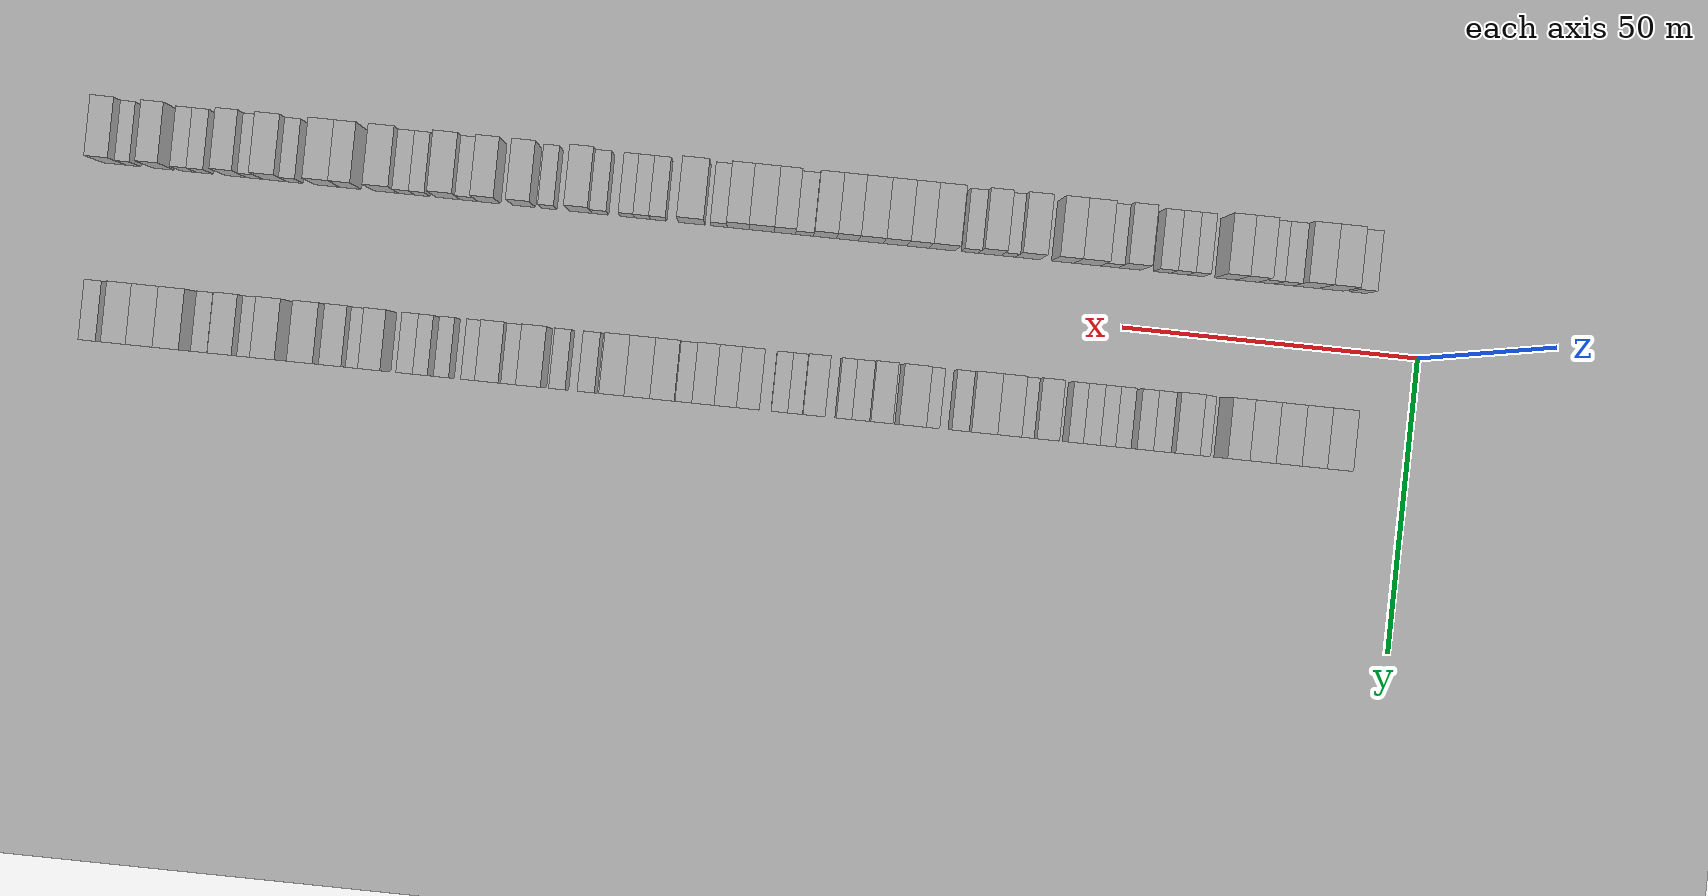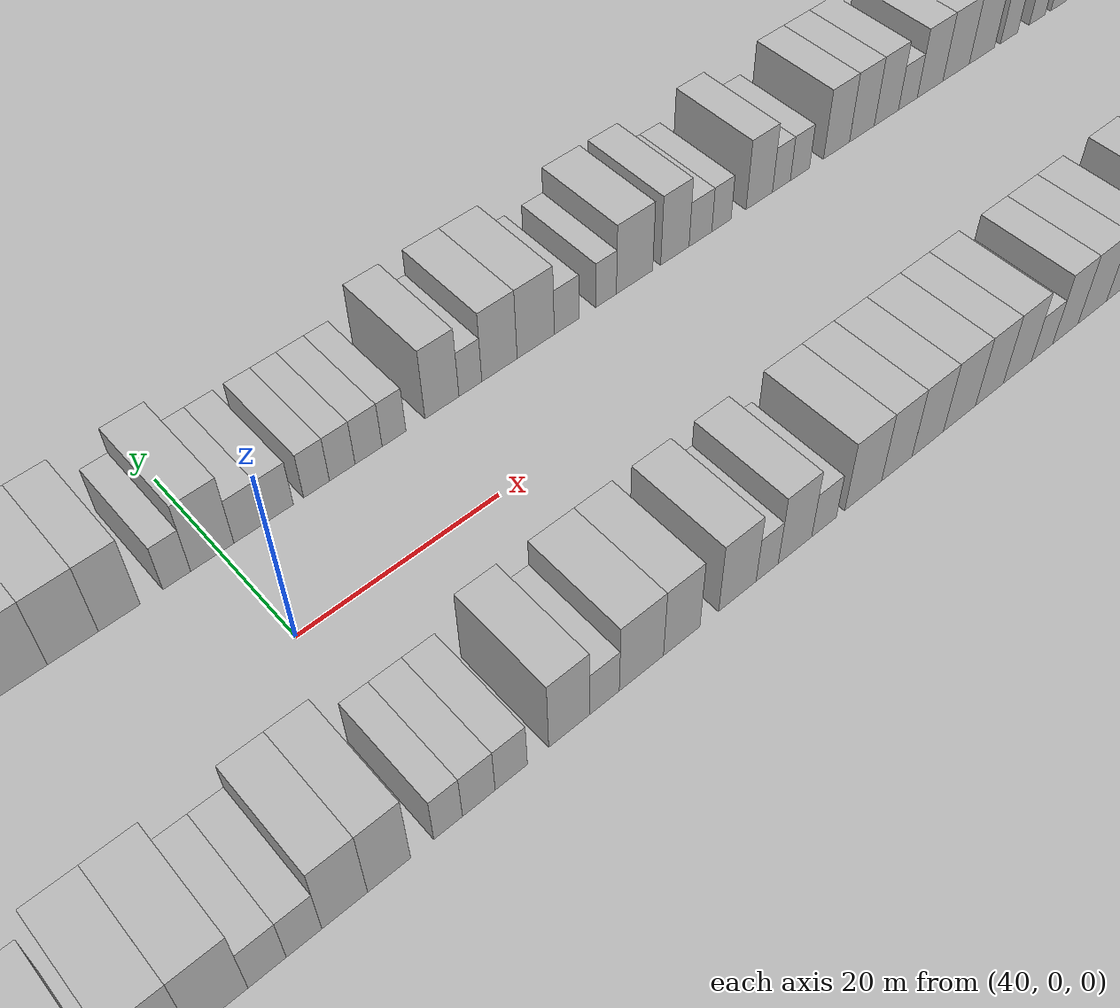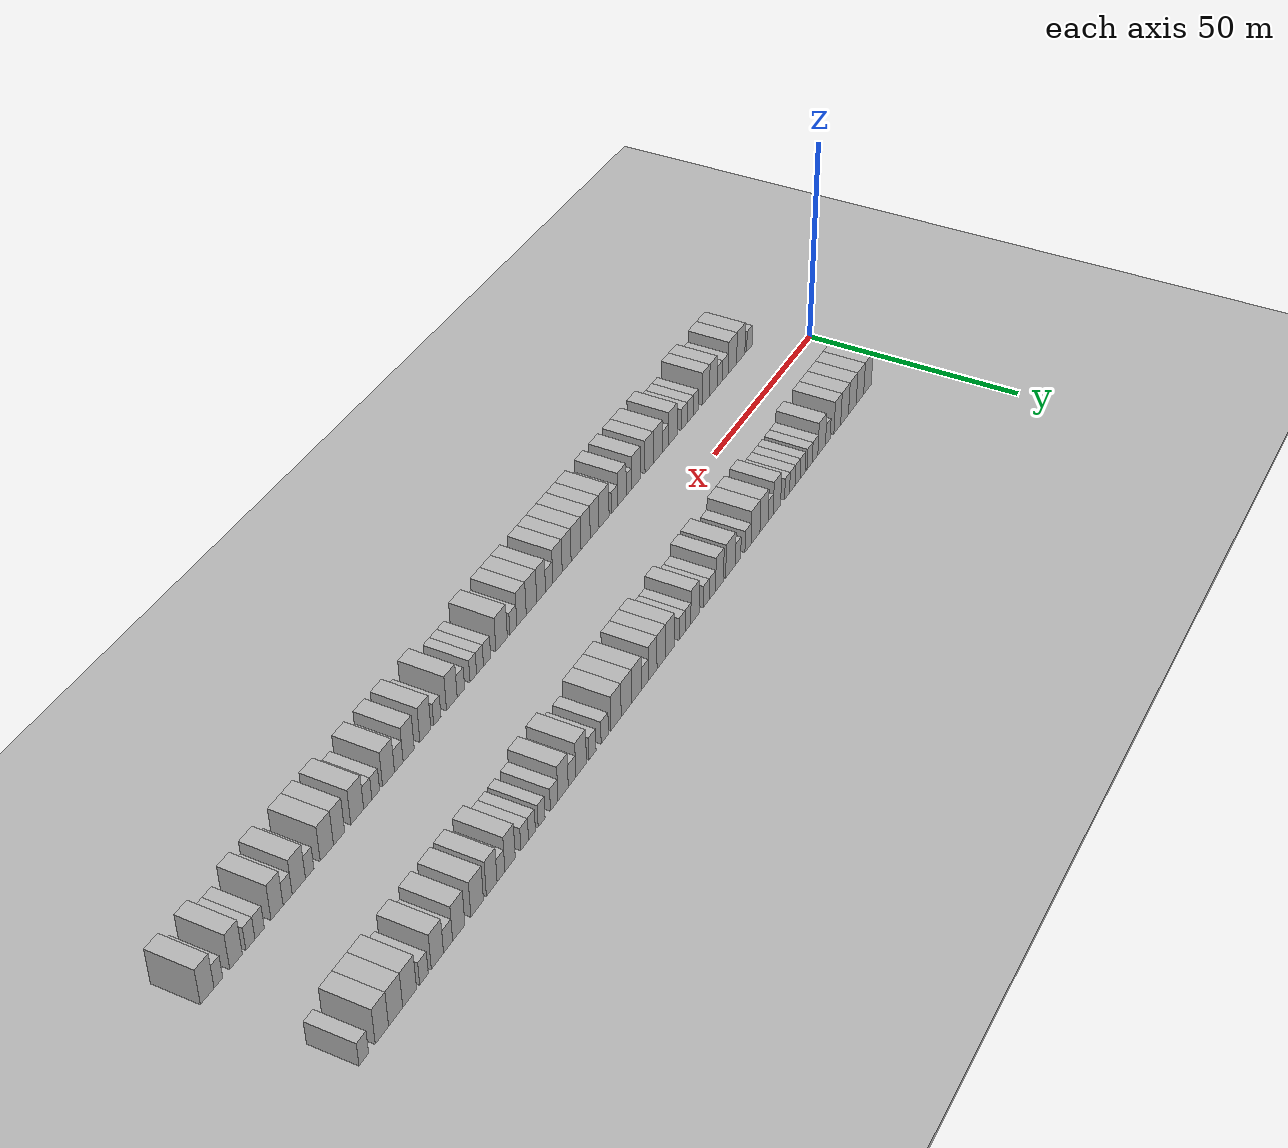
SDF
<?xml version="1.0" encoding="utf-8"?>

<sdf version="1.6">

   <world name="default">

      <gui fullscreen="0">

         <camera name="user_camera">

            <pose>-15 0 4.57585 0 0 0</pose>

            <view_controller>orbit</view_controller>

         </camera>

      </gui>

      <scene>

         <sky>

           <clouds>

             <speed>12</speed>

           </clouds>

         </sky>

         <ambient>0.4 0.4 0.4 1</ambient>

         <background>0.7 0.7 0.7 1</background>

         <shadows>1</shadows>

      </scene>

      <gravity>0 0 -9.8066</gravity>

      <magnetic_field>6e-06 2.3e-05 -4.2e-05</magnetic_field>

      <physics default="0" name="default_physics" type="ode">

         <ode>

            <solver>

               <type>quick</type>

               <iters>10</iters>

               <sor>1.0</sor>

               <use_dynamic_moi_rescaling>0</use_dynamic_moi_rescaling>

            </solver>

            <constraints>

               <cfm>0</cfm>

               <erp>0.2</erp>

               <contact_max_correcting_vel>100</contact_max_correcting_vel>

               <contact_surface_layer>0.001</contact_surface_layer>

            </constraints>

         </ode>

         <max_step_size>0.004</max_step_size>

         <real_time_factor>1</real_time_factor>

         <real_time_update_rate>250</real_time_update_rate>

      </physics>

      <light name="sun" type="directional">

         <cast_shadows>1</cast_shadows>

         <pose>0 0 10 0 0 0</pose>

         <diffuse>0.8 0.8 0.8 1</diffuse>

         <specular>0.2 0.2 0.2 1</specular>

         <attenuation>

            <range>1000</range>

            <constant>0.9</constant>

            <linear>0.01</linear>

            <quadratic>0.001</quadratic>

         </attenuation>

         <direction>-0.5 0.1 -0.9</direction>

      </light>

      <include>

         <name>ground_plane_1</name>

         <uri>model://HANNAS_ground_plane</uri>

         <pose>0 0 0  0 0 0</pose>

      </include>

      <include>

         <name>ground_plane_2</name>

         <uri>model://HANNAS_ground_plane</uri>

         <pose>100 0 0  0 0 0</pose>

      </include>

      <model name="building_1">

         <static>1</static>

         <pose frame="">14.1433 15.0000 0 0.000000 0.000000 1.570796</pose>

         <link name="link">

            <pose frame="">0 0 4.50 0 0 0</pose>

            <collision name="collision">

               <geometry>

                  <box>

                     <size>10.0000 4.2866 9.0000</size>

                  </box>

               </geometry>

               <max_contacts>10</max_contacts>

               <surface>

                  <contact>

                     <ode/>

                  </contact>

                  <bounce/>

                  <friction>

                     <torsional>

                        <ode/>

                     </torsional>

                     <ode/>

                  </friction>

               </surface>

            </collision>

            <visual name="visual">

               <cast_shadows>0</cast_shadows>

               <geometry>

                  <box>

                     <size>10.0000 4.2866 9.0000</size>

                  </box>

               </geometry>

               <material>

                  <script>

                     <uri>model://HANNAS_wall/materials/scripts</uri>

                     <uri>model://HANNAS_wall/materials/textures</uri>

                     <name>vrc/HANNAS_wall</name>

                  </script>

               </material>

            </visual>

            <self_collide>0</self_collide>

            <enable_wind>0</enable_wind>

            <kinematic>0</kinematic>

         </link>

      </model>

      <model name="building_2">

         <static>1</static>

         <pose frame="">18.3812 15.0000 0 0.000000 0.000000 1.570796</pose>

         <link name="link">

            <pose frame="">0 0 4.50 0 0 0</pose>

            <collision name="collision">

               <geometry>

                  <box>

                     <size>10.0000 4.1893 9.0000</size>

                  </box>

               </geometry>

               <max_contacts>10</max_contacts>

               <surface>

                  <contact>

                     <ode/>

                  </contact>

                  <bounce/>

                  <friction>

                     <torsional>

                        <ode/>

                     </torsional>

                     <ode/>

                  </friction>

               </surface>

            </collision>

            <visual name="visual">

               <cast_shadows>0</cast_shadows>

               <geometry>

                  <box>

                     <size>10.0000 4.1893 9.0000</size>

                  </box>

               </geometry>

               <material>

                  <script>

                     <uri>model://HANNAS_wall/materials/scripts</uri>

                     <uri>model://HANNAS_wall/materials/textures</uri>

                     <name>vrc/HANNAS_wall</name>

                  </script>

               </material>

            </visual>

            <self_collide>0</self_collide>

            <enable_wind>0</enable_wind>

            <kinematic>0</kinematic>

         </link>

      </model>

      <model name="building_3">

         <static>1</static>

         <pose frame="">22.5935 15.0000 0 0.000000 0.000000 1.570796</pose>

         <link name="link">

            <pose frame="">0 0 4.50 0 0 0</pose>

            <collision name="collision">

               <geometry>

                  <box>

                     <size>10.0000 4.2353 9.0000</size>

                  </box>

               </geometry>

               <max_contacts>10</max_contacts>

               <surface>

                  <contact>

                     <ode/>

                  </contact>

                  <bounce/>

                  <friction>

                     <torsional>

                        <ode/>

                     </torsional>

                     <ode/>

                  </friction>

               </surface>

            </collision>

            <visual name="visual">

               <cast_shadows>0</cast_shadows>

               <geometry>

                  <box>

                     <size>10.0000 4.2353 9.0000</size>

                  </box>

               </geometry>

               <material>

                  <script>

                     <uri>model://HANNAS_wall/materials/scripts</uri>

                     <uri>model://HANNAS_wall/materials/textures</uri>

                     <name>vrc/HANNAS_wall</name>

                  </script>

               </material>

            </visual>

            <self_collide>0</self_collide>

            <enable_wind>0</enable_wind>

            <kinematic>0</kinematic>

         </link>

      </model>

      <model name="building_4">

         <static>1</static>

         <pose frame="">26.8650 15.0000 0 0.000000 0.000000 1.570796</pose>

         <link name="link">

            <pose frame="">0 0 4.50 0 0 0</pose>

            <collision name="collision">

               <geometry>

                  <box>

                     <size>10.0000 4.3076 9.0000</size>

                  </box>

               </geometry>

               <max_contacts>10</max_contacts>

               <surface>

                  <contact>

                     <ode/>

                  </contact>

                  <bounce/>

                  <friction>

                     <torsional>

                        <ode/>

                     </torsional>

                     <ode/>

                  </friction>

               </surface>

            </collision>

            <visual name="visual">

               <cast_shadows>0</cast_shadows>

               <geometry>

                  <box>

                     <size>10.0000 4.3076 9.0000</size>

                  </box>

               </geometry>

               <material>

                  <script>

                     <uri>model://HANNAS_wall/materials/scripts</uri>

                     <uri>model://HANNAS_wall/materials/textures</uri>

                     <name>vrc/HANNAS_wall</name>

                  </script>

               </material>

            </visual>

            <self_collide>0</self_collide>

            <enable_wind>0</enable_wind>

            <kinematic>0</kinematic>

         </link>

      </model>

      <model name="building_5">

         <static>1</static>

         <pose frame="">30.8387 15.0000 0 0.000000 0.000000 1.570796</pose>

         <link name="link">

            <pose frame="">0 0 4.50 0 0 0</pose>

            <collision name="collision">

               <geometry>

                  <box>

                     <size>10.0000 3.6397 9.0000</size>

                  </box>

               </geometry>

               <max_contacts>10</max_contacts>

               <surface>

                  <contact>

                     <ode/>

                  </contact>

                  <bounce/>

                  <friction>

                     <torsional>

                        <ode/>

                     </torsional>

                     <ode/>

                  </friction>

               </surface>

            </collision>

            <visual name="visual">

               <cast_shadows>0</cast_shadows>

               <geometry>

                  <box>

                     <size>10.0000 3.6397 9.0000</size>

                  </box>

               </geometry>

               <material>

                  <script>

                     <uri>model://HANNAS_wall/materials/scripts</uri>

                     <uri>model://HANNAS_wall/materials/textures</uri>

                     <name>vrc/HANNAS_wall</name>

                  </script>

               </material>

            </visual>

            <self_collide>0</self_collide>

            <enable_wind>0</enable_wind>

            <kinematic>0</kinematic>

         </link>

      </model>

      <model name="building_6">

         <static>1</static>

         <pose frame="">35.9202 15.0000 0 0.000000 0.000000 1.570796</pose>

         <link name="link">

            <pose frame="">0 0 3.00 0 0 0</pose>

            <collision name="collision">

               <geometry>

                  <box>

                     <size>10.0000 2.5234 6.0000</size>

                  </box>

               </geometry>

               <max_contacts>10</max_contacts>

               <surface>

                  <contact>

                     <ode/>

                  </contact>

                  <bounce/>

                  <friction>

                     <torsional>

                        <ode/>

                     </torsional>

                     <ode/>

                  </friction>

               </surface>

            </collision>

            <visual name="visual">

               <cast_shadows>0</cast_shadows>

               <geometry>

                  <box>

                     <size>10.0000 2.5234 6.0000</size>

                  </box>

               </geometry>

               <material>

                  <script>

                     <uri>model://HANNAS_wall/materials/scripts</uri>

                     <uri>model://HANNAS_wall/materials/textures</uri>

                     <name>vrc/HANNAS_wall</name>

                  </script>

               </material>

            </visual>

            <self_collide>0</self_collide>

            <enable_wind>0</enable_wind>

            <kinematic>0</kinematic>

         </link>

      </model>

      <model name="building_7">

         <static>1</static>

         <pose frame="">39.1829 15.0000 0 0.000000 0.000000 1.570796</pose>

         <link name="link">

            <pose frame="">0 0 4.50 0 0 0</pose>

            <collision name="collision">

               <geometry>

                  <box>

                     <size>10.0000 4.0020 9.0000</size>

                  </box>

               </geometry>

               <max_contacts>10</max_contacts>

               <surface>

                  <contact>

                     <ode/>

                  </contact>

                  <bounce/>

                  <friction>

                     <torsional>

                        <ode/>

                     </torsional>

                     <ode/>

                  </friction>

               </surface>

            </collision>

            <visual name="visual">

               <cast_shadows>0</cast_shadows>

               <geometry>

                  <box>

                     <size>10.0000 4.0020 9.0000</size>

                  </box>

               </geometry>

               <material>

                  <script>

                     <uri>model://HANNAS_wall/materials/scripts</uri>

                     <uri>model://HANNAS_wall/materials/textures</uri>

                     <name>vrc/HANNAS_wall</name>

                  </script>

               </material>

            </visual>

            <self_collide>0</self_collide>

            <enable_wind>0</enable_wind>

            <kinematic>0</kinematic>

         </link>

      </model>

      <model name="building_8">

         <static>1</static>

         <pose frame="">42.6572 15.0000 0 0.000000 0.000000 1.570796</pose>

         <link name="link">

            <pose frame="">0 0 3.00 0 0 0</pose>

            <collision name="collision">

               <geometry>

                  <box>

                     <size>10.0000 2.9467 6.0000</size>

                  </box>

               </geometry>

               <max_contacts>10</max_contacts>

               <surface>

                  <contact>

                     <ode/>

                  </contact>

                  <bounce/>

                  <friction>

                     <torsional>

                        <ode/>

                     </torsional>

                     <ode/>

                  </friction>

               </surface>

            </collision>

            <visual name="visual">

               <cast_shadows>0</cast_shadows>

               <geometry>

                  <box>

                     <size>10.0000 2.9467 6.0000</size>

                  </box>

               </geometry>

               <material>

                  <script>

                     <uri>model://HANNAS_wall/materials/scripts</uri>

                     <uri>model://HANNAS_wall/materials/textures</uri>

                     <name>vrc/HANNAS_wall</name>

                  </script>

               </material>

            </visual>

            <self_collide>0</self_collide>

            <enable_wind>0</enable_wind>

            <kinematic>0</kinematic>

         </link>

      </model>

      <model name="building_9">

         <static>1</static>

         <pose frame="">45.4963 15.0000 0 0.000000 0.000000 1.570796</pose>

         <link name="link">

            <pose frame="">0 0 3.00 0 0 0</pose>

            <collision name="collision">

               <geometry>

                  <box>

                     <size>10.0000 2.7314 6.0000</size>

                  </box>

               </geometry>

               <max_contacts>10</max_contacts>

               <surface>

                  <contact>

                     <ode/>

                  </contact>

                  <bounce/>

                  <friction>

                     <torsional>

                        <ode/>

                     </torsional>

                     <ode/>

                  </friction>

               </surface>

            </collision>

            <visual name="visual">

               <cast_shadows>0</cast_shadows>

               <geometry>

                  <box>

                     <size>10.0000 2.7314 6.0000</size>

                  </box>

               </geometry>

               <material>

                  <script>

                     <uri>model://HANNAS_wall/materials/scripts</uri>

                     <uri>model://HANNAS_wall/materials/textures</uri>

                     <name>vrc/HANNAS_wall</name>

                  </script>

               </material>

            </visual>

            <self_collide>0</self_collide>

            <enable_wind>0</enable_wind>

            <kinematic>0</kinematic>

         </link>

      </model>

      <model name="building_10">

         <static>1</static>

         <pose frame="">49.1422 15.0000 0 0.000000 0.000000 1.570796</pose>

         <link name="link">

            <pose frame="">0 0 3.00 0 0 0</pose>

            <collision name="collision">

               <geometry>

                  <box>

                     <size>10.0000 2.5605 6.0000</size>

                  </box>

               </geometry>

               <max_contacts>10</max_contacts>

               <surface>

                  <contact>

                     <ode/>

                  </contact>

                  <bounce/>

                  <friction>

                     <torsional>

                        <ode/>

                     </torsional>

                     <ode/>

                  </friction>

               </surface>

            </collision>

            <visual name="visual">

               <cast_shadows>0</cast_shadows>

               <geometry>

                  <box>

                     <size>10.0000 2.5605 6.0000</size>

                  </box>

               </geometry>

               <material>

                  <script>

                     <uri>model://HANNAS_wall/materials/scripts</uri>

                     <uri>model://HANNAS_wall/materials/textures</uri>

                     <name>vrc/HANNAS_wall</name>

                  </script>

               </material>

            </visual>

            <self_collide>0</self_collide>

            <enable_wind>0</enable_wind>

            <kinematic>0</kinematic>

         </link>

      </model>

      <model name="building_11">

         <static>1</static>

         <pose frame="">51.7119 15.0000 0 0.000000 0.000000 1.570796</pose>

         <link name="link">

            <pose frame="">0 0 3.00 0 0 0</pose>

            <collision name="collision">

               <geometry>

                  <box>

                     <size>10.0000 2.5790 6.0000</size>

                  </box>

               </geometry>

               <max_contacts>10</max_contacts>

               <surface>

                  <contact>

                     <ode/>

                  </contact>

                  <bounce/>

                  <friction>

                     <torsional>

                        <ode/>

                     </torsional>

                     <ode/>

                  </friction>

               </surface>

            </collision>

            <visual name="visual">

               <cast_shadows>0</cast_shadows>

               <geometry>

                  <box>

                     <size>10.0000 2.5790 6.0000</size>

                  </box>

               </geometry>

               <material>

                  <script>

                     <uri>model://HANNAS_wall/materials/scripts</uri>

                     <uri>model://HANNAS_wall/materials/textures</uri>

                     <name>vrc/HANNAS_wall</name>

                  </script>

               </material>

            </visual>

            <self_collide>0</self_collide>

            <enable_wind>0</enable_wind>

            <kinematic>0</kinematic>

         </link>

      </model>

      <model name="building_12">

         <static>1</static>

         <pose frame="">54.3860 15.0000 0 0.000000 0.000000 1.570796</pose>

         <link name="link">

            <pose frame="">0 0 3.00 0 0 0</pose>

            <collision name="collision">

               <geometry>

                  <box>

                     <size>10.0000 2.7691 6.0000</size>

                  </box>

               </geometry>

               <max_contacts>10</max_contacts>

               <surface>

                  <contact>

                     <ode/>

                  </contact>

                  <bounce/>

                  <friction>

                     <torsional>

                        <ode/>

                     </torsional>

                     <ode/>

                  </friction>

               </surface>

            </collision>

            <visual name="visual">

               <cast_shadows>0</cast_shadows>

               <geometry>

                  <box>

                     <size>10.0000 2.7691 6.0000</size>

                  </box>

               </geometry>

               <material>

                  <script>

                     <uri>model://HANNAS_wall/materials/scripts</uri>

                     <uri>model://HANNAS_wall/materials/textures</uri>

                     <name>vrc/HANNAS_wall</name>

                  </script>

               </material>

            </visual>

            <self_collide>0</self_collide>

            <enable_wind>0</enable_wind>

            <kinematic>0</kinematic>

         </link>

      </model>

      <model name="building_13">

         <static>1</static>

         <pose frame="">57.0139 15.0000 0 0.000000 0.000000 1.570796</pose>

         <link name="link">

            <pose frame="">0 0 3.00 0 0 0</pose>

            <collision name="collision">

               <geometry>

                  <box>

                     <size>10.0000 2.4868 6.0000</size>

                  </box>

               </geometry>

               <max_contacts>10</max_contacts>

               <surface>

                  <contact>

                     <ode/>

                  </contact>

                  <bounce/>

                  <friction>

                     <torsional>

                        <ode/>

                     </torsional>

                     <ode/>

                  </friction>

               </surface>

            </collision>

            <visual name="visual">

               <cast_shadows>0</cast_shadows>

               <geometry>

                  <box>

                     <size>10.0000 2.4868 6.0000</size>

                  </box>

               </geometry>

               <material>

                  <script>

                     <uri>model://HANNAS_wall/materials/scripts</uri>

                     <uri>model://HANNAS_wall/materials/textures</uri>

                     <name>vrc/HANNAS_wall</name>

                  </script>

               </material>

            </visual>

            <self_collide>0</self_collide>

            <enable_wind>0</enable_wind>

            <kinematic>0</kinematic>

         </link>

      </model>

      <model name="building_14">

         <static>1</static>

         <pose frame="">62.0946 15.0000 0 0.000000 0.000000 1.570796</pose>

         <link name="link">

            <pose frame="">0 0 4.50 0 0 0</pose>

            <collision name="collision">

               <geometry>

                  <box>

                     <size>10.0000 3.6747 9.0000</size>

                  </box>

               </geometry>

               <max_contacts>10</max_contacts>

               <surface>

                  <contact>

                     <ode/>

                  </contact>

                  <bounce/>

                  <friction>

                     <torsional>

                        <ode/>

                     </torsional>

                     <ode/>

                  </friction>

               </surface>

            </collision>

            <visual name="visual">

               <cast_shadows>0</cast_shadows>

               <geometry>

                  <box>

                     <size>10.0000 3.6747 9.0000</size>

                  </box>

               </geometry>

               <material>

                  <script>

                     <uri>model://HANNAS_wall/materials/scripts</uri>

                     <uri>model://HANNAS_wall/materials/textures</uri>

                     <name>vrc/HANNAS_wall</name>

                  </script>

               </material>

            </visual>

            <self_collide>0</self_collide>

            <enable_wind>0</enable_wind>

            <kinematic>0</kinematic>

         </link>

      </model>

      <model name="building_15">

         <static>1</static>

         <pose frame="">65.1895 15.0000 0 0.000000 0.000000 1.570796</pose>

         <link name="link">

            <pose frame="">0 0 3.00 0 0 0</pose>

            <collision name="collision">

               <geometry>

                  <box>

                     <size>10.0000 2.5151 6.0000</size>

                  </box>

               </geometry>

               <max_contacts>10</max_contacts>

               <surface>

                  <contact>

                     <ode/>

                  </contact>

                  <bounce/>

                  <friction>

                     <torsional>

                        <ode/>

                     </torsional>

                     <ode/>

                  </friction>

               </surface>

            </collision>

            <visual name="visual">

               <cast_shadows>0</cast_shadows>

               <geometry>

                  <box>

                     <size>10.0000 2.5151 6.0000</size>

                  </box>

               </geometry>

               <material>

                  <script>

                     <uri>model://HANNAS_wall/materials/scripts</uri>

                     <uri>model://HANNAS_wall/materials/textures</uri>

                     <name>vrc/HANNAS_wall</name>

                  </script>

               </material>

            </visual>

            <self_collide>0</self_collide>

            <enable_wind>0</enable_wind>

            <kinematic>0</kinematic>

         </link>

      </model>

      <model name="building_16">

         <static>1</static>

         <pose frame="">68.4266 15.0000 0 0.000000 0.000000 1.570796</pose>

         <link name="link">

            <pose frame="">0 0 4.50 0 0 0</pose>

            <collision name="collision">

               <geometry>

                  <box>

                     <size>10.0000 3.9590 9.0000</size>

                  </box>

               </geometry>

               <max_contacts>10</max_contacts>

               <surface>

                  <contact>

                     <ode/>

                  </contact>

                  <bounce/>

                  <friction>

                     <torsional>

                        <ode/>

                     </torsional>

                     <ode/>

                  </friction>

               </surface>

            </collision>

            <visual name="visual">

               <cast_shadows>0</cast_shadows>

               <geometry>

                  <box>

                     <size>10.0000 3.9590 9.0000</size>

                  </box>

               </geometry>

               <material>

                  <script>

                     <uri>model://HANNAS_wall/materials/scripts</uri>

                     <uri>model://HANNAS_wall/materials/textures</uri>

                     <name>vrc/HANNAS_wall</name>

                  </script>

               </material>

            </visual>

            <self_collide>0</self_collide>

            <enable_wind>0</enable_wind>

            <kinematic>0</kinematic>

         </link>

      </model>

      <model name="building_17">

         <static>1</static>

         <pose frame="">72.5462 15.0000 0 0.000000 0.000000 1.570796</pose>

         <link name="link">

            <pose frame="">0 0 4.50 0 0 0</pose>

            <collision name="collision">

               <geometry>

                  <box>

                     <size>10.0000 4.2803 9.0000</size>

                  </box>

               </geometry>

               <max_contacts>10</max_contacts>

               <surface>

                  <contact>

                     <ode/>

                  </contact>

                  <bounce/>

                  <friction>

                     <torsional>

                        <ode/>

                     </torsional>

                     <ode/>

                  </friction>

               </surface>

            </collision>

            <visual name="visual">

               <cast_shadows>0</cast_shadows>

               <geometry>

                  <box>

                     <size>10.0000 4.2803 9.0000</size>

                  </box>

               </geometry>

               <material>

                  <script>

                     <uri>model://HANNAS_wall/materials/scripts</uri>

                     <uri>model://HANNAS_wall/materials/textures</uri>

                     <name>vrc/HANNAS_wall</name>

                  </script>

               </material>

            </visual>

            <self_collide>0</self_collide>

            <enable_wind>0</enable_wind>

            <kinematic>0</kinematic>

         </link>

      </model>

      <model name="building_18">

         <static>1</static>

         <pose frame="">76.1411 15.0000 0 0.000000 0.000000 1.570796</pose>

         <link name="link">

            <pose frame="">0 0 3.00 0 0 0</pose>

            <collision name="collision">

               <geometry>

                  <box>

                     <size>10.0000 2.9094 6.0000</size>

                  </box>

               </geometry>

               <max_contacts>10</max_contacts>

               <surface>

                  <contact>

                     <ode/>

                  </contact>

                  <bounce/>

                  <friction>

                     <torsional>

                        <ode/>

                     </torsional>

                     <ode/>

                  </friction>

               </surface>

            </collision>

            <visual name="visual">

               <cast_shadows>0</cast_shadows>

               <geometry>

                  <box>

                     <size>10.0000 2.9094 6.0000</size>

                  </box>

               </geometry>

               <material>

                  <script>

                     <uri>model://HANNAS_wall/materials/scripts</uri>

                     <uri>model://HANNAS_wall/materials/textures</uri>

                     <name>vrc/HANNAS_wall</name>

                  </script>

               </material>

            </visual>

            <self_collide>0</self_collide>

            <enable_wind>0</enable_wind>

            <kinematic>0</kinematic>

         </link>

      </model>

      <model name="building_19">

         <static>1</static>

         <pose frame="">80.8462 15.0000 0 0.000000 0.000000 1.570796</pose>

         <link name="link">

            <pose frame="">0 0 3.00 0 0 0</pose>

            <collision name="collision">

               <geometry>

                  <box>

                     <size>10.0000 2.5008 6.0000</size>

                  </box>

               </geometry>

               <max_contacts>10</max_contacts>

               <surface>

                  <contact>

                     <ode/>

                  </contact>

                  <bounce/>

                  <friction>

                     <torsional>

                        <ode/>

                     </torsional>

                     <ode/>

                  </friction>

               </surface>

            </collision>

            <visual name="visual">

               <cast_shadows>0</cast_shadows>

               <geometry>

                  <box>

                     <size>10.0000 2.5008 6.0000</size>

                  </box>

               </geometry>

               <material>

                  <script>

                     <uri>model://HANNAS_wall/materials/scripts</uri>

                     <uri>model://HANNAS_wall/materials/textures</uri>

                     <name>vrc/HANNAS_wall</name>

                  </script>

               </material>

            </visual>

            <self_collide>0</self_collide>

            <enable_wind>0</enable_wind>

            <kinematic>0</kinematic>

         </link>

      </model>

      <model name="building_20">

         <static>1</static>

         <pose frame="">84.3462 15.0000 0 0.000000 0.000000 1.570796</pose>

         <link name="link">

            <pose frame="">0 0 4.50 0 0 0</pose>

            <collision name="collision">

               <geometry>

                  <box>

                     <size>10.0000 4.4993 9.0000</size>

                  </box>

               </geometry>

               <max_contacts>10</max_contacts>

               <surface>

                  <contact>

                     <ode/>

                  </contact>

                  <bounce/>

                  <friction>

                     <torsional>

                        <ode/>

                     </torsional>

                     <ode/>

                  </friction>

               </surface>

            </collision>

            <visual name="visual">

               <cast_shadows>0</cast_shadows>

               <geometry>

                  <box>

                     <size>10.0000 4.4993 9.0000</size>

                  </box>

               </geometry>

               <material>

                  <script>

                     <uri>model://HANNAS_wall/materials/scripts</uri>

                     <uri>model://HANNAS_wall/materials/textures</uri>

                     <name>vrc/HANNAS_wall</name>

                  </script>

               </material>

            </visual>

            <self_collide>0</self_collide>

            <enable_wind>0</enable_wind>

            <kinematic>0</kinematic>

         </link>

      </model>

      <model name="building_21">

         <static>1</static>

         <pose frame="">89.4073 15.0000 0 0.000000 0.000000 1.570796</pose>

         <link name="link">

            <pose frame="">0 0 4.50 0 0 0</pose>

            <collision name="collision">

               <geometry>

                  <box>

                     <size>10.0000 3.6229 9.0000</size>

                  </box>

               </geometry>

               <max_contacts>10</max_contacts>

               <surface>

                  <contact>

                     <ode/>

                  </contact>

                  <bounce/>

                  <friction>

                     <torsional>

                        <ode/>

                     </torsional>

                     <ode/>

                  </friction>

               </surface>

            </collision>

            <visual name="visual">

               <cast_shadows>0</cast_shadows>

               <geometry>

                  <box>

                     <size>10.0000 3.6229 9.0000</size>

                  </box>

               </geometry>

               <material>

                  <script>

                     <uri>model://HANNAS_wall/materials/scripts</uri>

                     <uri>model://HANNAS_wall/materials/textures</uri>

                     <name>vrc/HANNAS_wall</name>

                  </script>

               </material>

            </visual>

            <self_collide>0</self_collide>

            <enable_wind>0</enable_wind>

            <kinematic>0</kinematic>

         </link>

      </model>

      <model name="building_22">

         <static>1</static>

         <pose frame="">92.6987 15.0000 0 0.000000 0.000000 1.570796</pose>

         <link name="link">

            <pose frame="">0 0 3.00 0 0 0</pose>

            <collision name="collision">

               <geometry>

                  <box>

                     <size>10.0000 2.9599 6.0000</size>

                  </box>

               </geometry>

               <max_contacts>10</max_contacts>

               <surface>

                  <contact>

                     <ode/>

                  </contact>

                  <bounce/>

                  <friction>

                     <torsional>

                        <ode/>

                     </torsional>

                     <ode/>

                  </friction>

               </surface>

            </collision>

            <visual name="visual">

               <cast_shadows>0</cast_shadows>

               <geometry>

                  <box>

                     <size>10.0000 2.9599 6.0000</size>

                  </box>

               </geometry>

               <material>

                  <script>

                     <uri>model://HANNAS_wall/materials/scripts</uri>

                     <uri>model://HANNAS_wall/materials/textures</uri>

                     <name>vrc/HANNAS_wall</name>

                  </script>

               </material>

            </visual>

            <self_collide>0</self_collide>

            <enable_wind>0</enable_wind>

            <kinematic>0</kinematic>

         </link>

      </model>

      <model name="building_23">

         <static>1</static>

         <pose frame="">95.4585 15.0000 0 0.000000 0.000000 1.570796</pose>

         <link name="link">

            <pose frame="">0 0 3.00 0 0 0</pose>

            <collision name="collision">

               <geometry>

                  <box>

                     <size>10.0000 2.5597 6.0000</size>

                  </box>

               </geometry>

               <max_contacts>10</max_contacts>

               <surface>

                  <contact>

                     <ode/>

                  </contact>

                  <bounce/>

                  <friction>

                     <torsional>

                        <ode/>

                     </torsional>

                     <ode/>

                  </friction>

               </surface>

            </collision>

            <visual name="visual">

               <cast_shadows>0</cast_shadows>

               <geometry>

                  <box>

                     <size>10.0000 2.5597 6.0000</size>

                  </box>

               </geometry>

               <material>

                  <script>

                     <uri>model://HANNAS_wall/materials/scripts</uri>

                     <uri>model://HANNAS_wall/materials/textures</uri>

                     <name>vrc/HANNAS_wall</name>

                  </script>

               </material>

            </visual>

            <self_collide>0</self_collide>

            <enable_wind>0</enable_wind>

            <kinematic>0</kinematic>

         </link>

      </model>

      <model name="building_24">

         <static>1</static>

         <pose frame="">100.5434 15.0000 0 0.000000 0.000000 1.570796</pose>

         <link name="link">

            <pose frame="">0 0 4.50 0 0 0</pose>

            <collision name="collision">

               <geometry>

                  <box>

                     <size>10.0000 3.6101 9.0000</size>

                  </box>

               </geometry>

               <max_contacts>10</max_contacts>

               <surface>

                  <contact>

                     <ode/>

                  </contact>

                  <bounce/>

                  <friction>

                     <torsional>

                        <ode/>

                     </torsional>

                     <ode/>

                  </friction>

               </surface>

            </collision>

            <visual name="visual">

               <cast_shadows>0</cast_shadows>

               <geometry>

                  <box>

                     <size>10.0000 3.6101 9.0000</size>

                  </box>

               </geometry>

               <material>

                  <script>

                     <uri>model://HANNAS_wall/materials/scripts</uri>

                     <uri>model://HANNAS_wall/materials/textures</uri>

                     <name>vrc/HANNAS_wall</name>

                  </script>

               </material>

            </visual>

            <self_collide>0</self_collide>

            <enable_wind>0</enable_wind>

            <kinematic>0</kinematic>

         </link>

      </model>

      <model name="building_25">

         <static>1</static>

         <pose frame="">103.5877 15.0000 0 0.000000 0.000000 1.570796</pose>

         <link name="link">

            <pose frame="">0 0 3.00 0 0 0</pose>

            <collision name="collision">

               <geometry>

                  <box>

                     <size>10.0000 2.4786 6.0000</size>

                  </box>

               </geometry>

               <max_contacts>10</max_contacts>

               <surface>

                  <contact>

                     <ode/>

                  </contact>

                  <bounce/>

                  <friction>

                     <torsional>

                        <ode/>

                     </torsional>

                     <ode/>

                  </friction>

               </surface>

            </collision>

            <visual name="visual">

               <cast_shadows>0</cast_shadows>

               <geometry>

                  <box>

                     <size>10.0000 2.4786 6.0000</size>

                  </box>

               </geometry>

               <material>

                  <script>

                     <uri>model://HANNAS_wall/materials/scripts</uri>

                     <uri>model://HANNAS_wall/materials/textures</uri>

                     <name>vrc/HANNAS_wall</name>

                  </script>

               </material>

            </visual>

            <self_collide>0</self_collide>

            <enable_wind>0</enable_wind>

            <kinematic>0</kinematic>

         </link>

      </model>

      <model name="building_26">

         <static>1</static>

         <pose frame="">106.1811 15.0000 0 0.000000 0.000000 1.570796</pose>

         <link name="link">

            <pose frame="">0 0 3.00 0 0 0</pose>

            <collision name="collision">

               <geometry>

                  <box>

                     <size>10.0000 2.7080 6.0000</size>

                  </box>

               </geometry>

               <max_contacts>10</max_contacts>

               <surface>

                  <contact>

                     <ode/>

                  </contact>

                  <bounce/>

                  <friction>

                     <torsional>

                        <ode/>

                     </torsional>

                     <ode/>

                  </friction>

               </surface>

            </collision>

            <visual name="visual">

               <cast_shadows>0</cast_shadows>

               <geometry>

                  <box>

                     <size>10.0000 2.7080 6.0000</size>

                  </box>

               </geometry>

               <material>

                  <script>

                     <uri>model://HANNAS_wall/materials/scripts</uri>

                     <uri>model://HANNAS_wall/materials/textures</uri>

                     <name>vrc/HANNAS_wall</name>

                  </script>

               </material>

            </visual>

            <self_collide>0</self_collide>

            <enable_wind>0</enable_wind>

            <kinematic>0</kinematic>

         </link>

      </model>

      <model name="building_27">

         <static>1</static>

         <pose frame="">111.4133 15.0000 0 0.000000 0.000000 1.570796</pose>

         <link name="link">

            <pose frame="">0 0 4.50 0 0 0</pose>

            <collision name="collision">

               <geometry>

                  <box>

                     <size>10.0000 3.7564 9.0000</size>

                  </box>

               </geometry>

               <max_contacts>10</max_contacts>

               <surface>

                  <contact>

                     <ode/>

                  </contact>

                  <bounce/>

                  <friction>

                     <torsional>

                        <ode/>

                     </torsional>

                     <ode/>

                  </friction>

               </surface>

            </collision>

            <visual name="visual">

               <cast_shadows>0</cast_shadows>

               <geometry>

                  <box>

                     <size>10.0000 3.7564 9.0000</size>

                  </box>

               </geometry>

               <material>

                  <script>

                     <uri>model://HANNAS_wall/materials/scripts</uri>

                     <uri>model://HANNAS_wall/materials/textures</uri>

                     <name>vrc/HANNAS_wall</name>

                  </script>

               </material>

            </visual>

            <self_collide>0</self_collide>

            <enable_wind>0</enable_wind>

            <kinematic>0</kinematic>

         </link>

      </model>

      <model name="building_28">

         <static>1</static>

         <pose frame="">115.1273 15.0000 0 0.000000 0.000000 1.570796</pose>

         <link name="link">

            <pose frame="">0 0 4.50 0 0 0</pose>

            <collision name="collision">

               <geometry>

                  <box>

                     <size>10.0000 3.6715 9.0000</size>

                  </box>

               </geometry>

               <max_contacts>10</max_contacts>

               <surface>

                  <contact>

                     <ode/>

                  </contact>

                  <bounce/>

                  <friction>

                     <torsional>

                        <ode/>

                     </torsional>

                     <ode/>

                  </friction>

               </surface>

            </collision>

            <visual name="visual">

               <cast_shadows>0</cast_shadows>

               <geometry>

                  <box>

                     <size>10.0000 3.6715 9.0000</size>

                  </box>

               </geometry>

               <material>

                  <script>

                     <uri>model://HANNAS_wall/materials/scripts</uri>

                     <uri>model://HANNAS_wall/materials/textures</uri>

                     <name>vrc/HANNAS_wall</name>

                  </script>

               </material>

            </visual>

            <self_collide>0</self_collide>

            <enable_wind>0</enable_wind>

            <kinematic>0</kinematic>

         </link>

      </model>

      <model name="building_29">

         <static>1</static>

         <pose frame="">118.7872 15.0000 0 0.000000 0.000000 1.570796</pose>

         <link name="link">

            <pose frame="">0 0 4.50 0 0 0</pose>

            <collision name="collision">

               <geometry>

                  <box>

                     <size>10.0000 3.6483 9.0000</size>

                  </box>

               </geometry>

               <max_contacts>10</max_contacts>

               <surface>

                  <contact>

                     <ode/>

                  </contact>

                  <bounce/>

                  <friction>

                     <torsional>

                        <ode/>

                     </torsional>

                     <ode/>

                  </friction>

               </surface>

            </collision>

            <visual name="visual">

               <cast_shadows>0</cast_shadows>

               <geometry>

                  <box>

                     <size>10.0000 3.6483 9.0000</size>

                  </box>

               </geometry>

               <material>

                  <script>

                     <uri>model://HANNAS_wall/materials/scripts</uri>

                     <uri>model://HANNAS_wall/materials/textures</uri>

                     <name>vrc/HANNAS_wall</name>

                  </script>

               </material>

            </visual>

            <self_collide>0</self_collide>

            <enable_wind>0</enable_wind>

            <kinematic>0</kinematic>

         </link>

      </model>

      <model name="building_30">

         <static>1</static>

         <pose frame="">122.0579 15.0000 0 0.000000 0.000000 1.570796</pose>

         <link name="link">

            <pose frame="">0 0 3.00 0 0 0</pose>

            <collision name="collision">

               <geometry>

                  <box>

                     <size>10.0000 2.8931 6.0000</size>

                  </box>

               </geometry>

               <max_contacts>10</max_contacts>

               <surface>

                  <contact>

                     <ode/>

                  </contact>

                  <bounce/>

                  <friction>

                     <torsional>

                        <ode/>

                     </torsional>

                     <ode/>

                  </friction>

               </surface>

            </collision>

            <visual name="visual">

               <cast_shadows>0</cast_shadows>

               <geometry>

                  <box>

                     <size>10.0000 2.8931 6.0000</size>

                  </box>

               </geometry>

               <material>

                  <script>

                     <uri>model://HANNAS_wall/materials/scripts</uri>

                     <uri>model://HANNAS_wall/materials/textures</uri>

                     <name>vrc/HANNAS_wall</name>

                  </script>

               </material>

            </visual>

            <self_collide>0</self_collide>

            <enable_wind>0</enable_wind>

            <kinematic>0</kinematic>

         </link>

      </model>

      <model name="building_31">

         <static>1</static>

         <pose frame="">125.5207 15.0000 0 0.000000 0.000000 1.570796</pose>

         <link name="link">

            <pose frame="">0 0 4.50 0 0 0</pose>

            <collision name="collision">

               <geometry>

                  <box>

                     <size>10.0000 4.0324 9.0000</size>

                  </box>

               </geometry>

               <max_contacts>10</max_contacts>

               <surface>

                  <contact>

                     <ode/>

                  </contact>

                  <bounce/>

                  <friction>

                     <torsional>

                        <ode/>

                     </torsional>

                     <ode/>

                  </friction>

               </surface>

            </collision>

            <visual name="visual">

               <cast_shadows>0</cast_shadows>

               <geometry>

                  <box>

                     <size>10.0000 4.0324 9.0000</size>

                  </box>

               </geometry>

               <material>

                  <script>

                     <uri>model://HANNAS_wall/materials/scripts</uri>

                     <uri>model://HANNAS_wall/materials/textures</uri>

                     <name>vrc/HANNAS_wall</name>

                  </script>

               </material>

            </visual>

            <self_collide>0</self_collide>

            <enable_wind>0</enable_wind>

            <kinematic>0</kinematic>

         </link>

      </model>

      <model name="building_32">

         <static>1</static>

         <pose frame="">129.6454 15.0000 0 0.000000 0.000000 1.570796</pose>

         <link name="link">

            <pose frame="">0 0 4.50 0 0 0</pose>

            <collision name="collision">

               <geometry>

                  <box>

                     <size>10.0000 4.2172 9.0000</size>

                  </box>

               </geometry>

               <max_contacts>10</max_contacts>

               <surface>

                  <contact>

                     <ode/>

                  </contact>

                  <bounce/>

                  <friction>

                     <torsional>

                        <ode/>

                     </torsional>

                     <ode/>

                  </friction>

               </surface>

            </collision>

            <visual name="visual">

               <cast_shadows>0</cast_shadows>

               <geometry>

                  <box>

                     <size>10.0000 4.2172 9.0000</size>

                  </box>

               </geometry>

               <material>

                  <script>

                     <uri>model://HANNAS_wall/materials/scripts</uri>

                     <uri>model://HANNAS_wall/materials/textures</uri>

                     <name>vrc/HANNAS_wall</name>

                  </script>

               </material>

            </visual>

            <self_collide>0</self_collide>

            <enable_wind>0</enable_wind>

            <kinematic>0</kinematic>

         </link>

      </model>

      <model name="building_33">

         <static>1</static>

         <pose frame="">133.8189 15.0000 0 0.000000 0.000000 1.570796</pose>

         <link name="link">

            <pose frame="">0 0 4.50 0 0 0</pose>

            <collision name="collision">

               <geometry>

                  <box>

                     <size>10.0000 4.1298 9.0000</size>

                  </box>

               </geometry>

               <max_contacts>10</max_contacts>

               <surface>

                  <contact>

                     <ode/>

                  </contact>

                  <bounce/>

                  <friction>

                     <torsional>

                        <ode/>

                     </torsional>

                     <ode/>

                  </friction>

               </surface>

            </collision>

            <visual name="visual">

               <cast_shadows>0</cast_shadows>

               <geometry>

                  <box>

                     <size>10.0000 4.1298 9.0000</size>

                  </box>

               </geometry>

               <material>

                  <script>

                     <uri>model://HANNAS_wall/materials/scripts</uri>

                     <uri>model://HANNAS_wall/materials/textures</uri>

                     <name>vrc/HANNAS_wall</name>

                  </script>

               </material>

            </visual>

            <self_collide>0</self_collide>

            <enable_wind>0</enable_wind>

            <kinematic>0</kinematic>

         </link>

      </model>

      <model name="building_34">

         <static>1</static>

         <pose frame="">138.3126 15.0000 0 0.000000 0.000000 1.570796</pose>

         <link name="link">

            <pose frame="">0 0 3.00 0 0 0</pose>

            <collision name="collision">

               <geometry>

                  <box>

                     <size>10.0000 2.8577 6.0000</size>

                  </box>

               </geometry>

               <max_contacts>10</max_contacts>

               <surface>

                  <contact>

                     <ode/>

                  </contact>

                  <bounce/>

                  <friction>

                     <torsional>

                        <ode/>

                     </torsional>

                     <ode/>

                  </friction>

               </surface>

            </collision>

            <visual name="visual">

               <cast_shadows>0</cast_shadows>

               <geometry>

                  <box>

                     <size>10.0000 2.8577 6.0000</size>

                  </box>

               </geometry>

               <material>

                  <script>

                     <uri>model://HANNAS_wall/materials/scripts</uri>

                     <uri>model://HANNAS_wall/materials/textures</uri>

                     <name>vrc/HANNAS_wall</name>

                  </script>

               </material>

            </visual>

            <self_collide>0</self_collide>

            <enable_wind>0</enable_wind>

            <kinematic>0</kinematic>

         </link>

      </model>

      <model name="building_35">

         <static>1</static>

         <pose frame="">143.1070 15.0000 0 0.000000 0.000000 1.570796</pose>

         <link name="link">

            <pose frame="">0 0 3.00 0 0 0</pose>

            <collision name="collision">

               <geometry>

                  <box>

                     <size>10.0000 2.7310 6.0000</size>

                  </box>

               </geometry>

               <max_contacts>10</max_contacts>

               <surface>

                  <contact>

                     <ode/>

                  </contact>

                  <bounce/>

                  <friction>

                     <torsional>

                        <ode/>

                     </torsional>

                     <ode/>

                  </friction>

               </surface>

            </collision>

            <visual name="visual">

               <cast_shadows>0</cast_shadows>

               <geometry>

                  <box>

                     <size>10.0000 2.7310 6.0000</size>

                  </box>

               </geometry>

               <material>

                  <script>

                     <uri>model://HANNAS_wall/materials/scripts</uri>

                     <uri>model://HANNAS_wall/materials/textures</uri>

                     <name>vrc/HANNAS_wall</name>

                  </script>

               </material>

            </visual>

            <self_collide>0</self_collide>

            <enable_wind>0</enable_wind>

            <kinematic>0</kinematic>

         </link>

      </model>

      <model name="building_36">

         <static>1</static>

         <pose frame="">147.5088 15.0000 0 0.000000 0.000000 1.570796</pose>

         <link name="link">

            <pose frame="">0 0 4.50 0 0 0</pose>

            <collision name="collision">

               <geometry>

                  <box>

                     <size>10.0000 4.0727 9.0000</size>

                  </box>

               </geometry>

               <max_contacts>10</max_contacts>

               <surface>

                  <contact>

                     <ode/>

                  </contact>

                  <bounce/>

                  <friction>

                     <torsional>

                        <ode/>

                     </torsional>

                     <ode/>

                  </friction>

               </surface>

            </collision>

            <visual name="visual">

               <cast_shadows>0</cast_shadows>

               <geometry>

                  <box>

                     <size>10.0000 4.0727 9.0000</size>

                  </box>

               </geometry>

               <material>

                  <script>

                     <uri>model://HANNAS_wall/materials/scripts</uri>

                     <uri>model://HANNAS_wall/materials/textures</uri>

                     <name>vrc/HANNAS_wall</name>

                  </script>

               </material>

            </visual>

            <self_collide>0</self_collide>

            <enable_wind>0</enable_wind>

            <kinematic>0</kinematic>

         </link>

      </model>

      <model name="building_37">

         <static>1</static>

         <pose frame="">150.9793 15.0000 0 0.000000 0.000000 1.570796</pose>

         <link name="link">

            <pose frame="">0 0 3.00 0 0 0</pose>

            <collision name="collision">

               <geometry>

                  <box>

                     <size>10.0000 2.8682 6.0000</size>

                  </box>

               </geometry>

               <max_contacts>10</max_contacts>

               <surface>

                  <contact>

                     <ode/>

                  </contact>

                  <bounce/>

                  <friction>

                     <torsional>

                        <ode/>

                     </torsional>

                     <ode/>

                  </friction>

               </surface>

            </collision>

            <visual name="visual">

               <cast_shadows>0</cast_shadows>

               <geometry>

                  <box>

                     <size>10.0000 2.8682 6.0000</size>

                  </box>

               </geometry>

               <material>

                  <script>

                     <uri>model://HANNAS_wall/materials/scripts</uri>

                     <uri>model://HANNAS_wall/materials/textures</uri>

                     <name>vrc/HANNAS_wall</name>

                  </script>

               </material>

            </visual>

            <self_collide>0</self_collide>

            <enable_wind>0</enable_wind>

            <kinematic>0</kinematic>

         </link>

      </model>

      <model name="building_38">

         <static>1</static>

         <pose frame="">154.3399 15.0000 0 0.000000 0.000000 1.570796</pose>

         <link name="link">

            <pose frame="">0 0 4.50 0 0 0</pose>

            <collision name="collision">

               <geometry>

                  <box>

                     <size>10.0000 3.8530 9.0000</size>

                  </box>

               </geometry>

               <max_contacts>10</max_contacts>

               <surface>

                  <contact>

                     <ode/>

                  </contact>

                  <bounce/>

                  <friction>

                     <torsional>

                        <ode/>

                     </torsional>

                     <ode/>

                  </friction>

               </surface>

            </collision>

            <visual name="visual">

               <cast_shadows>0</cast_shadows>

               <geometry>

                  <box>

                     <size>10.0000 3.8530 9.0000</size>

                  </box>

               </geometry>

               <material>

                  <script>

                     <uri>model://HANNAS_wall/materials/scripts</uri>

                     <uri>model://HANNAS_wall/materials/textures</uri>

                     <name>vrc/HANNAS_wall</name>

                  </script>

               </material>

            </visual>

            <self_collide>0</self_collide>

            <enable_wind>0</enable_wind>

            <kinematic>0</kinematic>

         </link>

      </model>

      <model name="building_39">

         <static>1</static>

         <pose frame="">157.6672 15.0000 0 0.000000 0.000000 1.570796</pose>

         <link name="link">

            <pose frame="">0 0 3.00 0 0 0</pose>

            <collision name="collision">

               <geometry>

                  <box>

                     <size>10.0000 2.8016 6.0000</size>

                  </box>

               </geometry>

               <max_contacts>10</max_contacts>

               <surface>

                  <contact>

                     <ode/>

                  </contact>

                  <bounce/>

                  <friction>

                     <torsional>

                        <ode/>

                     </torsional>

                     <ode/>

                  </friction>

               </surface>

            </collision>

            <visual name="visual">

               <cast_shadows>0</cast_shadows>

               <geometry>

                  <box>

                     <size>10.0000 2.8016 6.0000</size>

                  </box>

               </geometry>

               <material>

                  <script>

                     <uri>model://HANNAS_wall/materials/scripts</uri>

                     <uri>model://HANNAS_wall/materials/textures</uri>

                     <name>vrc/HANNAS_wall</name>

                  </script>

               </material>

            </visual>

            <self_collide>0</self_collide>

            <enable_wind>0</enable_wind>

            <kinematic>0</kinematic>

         </link>

      </model>

      <model name="building_40">

         <static>1</static>

         <pose frame="">162.3288 15.0000 0 0.000000 0.000000 1.570796</pose>

         <link name="link">

            <pose frame="">0 0 3.00 0 0 0</pose>

            <collision name="collision">

               <geometry>

                  <box>

                     <size>10.0000 2.5216 6.0000</size>

                  </box>

               </geometry>

               <max_contacts>10</max_contacts>

               <surface>

                  <contact>

                     <ode/>

                  </contact>

                  <bounce/>

                  <friction>

                     <torsional>

                        <ode/>

                     </torsional>

                     <ode/>

                  </friction>

               </surface>

            </collision>

            <visual name="visual">

               <cast_shadows>0</cast_shadows>

               <geometry>

                  <box>

                     <size>10.0000 2.5216 6.0000</size>

                  </box>

               </geometry>

               <material>

                  <script>

                     <uri>model://HANNAS_wall/materials/scripts</uri>

                     <uri>model://HANNAS_wall/materials/textures</uri>

                     <name>vrc/HANNAS_wall</name>

                  </script>

               </material>

            </visual>

            <self_collide>0</self_collide>

            <enable_wind>0</enable_wind>

            <kinematic>0</kinematic>

         </link>

      </model>

      <model name="building_41">

         <static>1</static>

         <pose frame="">165.8322 15.0000 0 0.000000 0.000000 1.570796</pose>

         <link name="link">

            <pose frame="">0 0 3.00 0 0 0</pose>

            <collision name="collision">

               <geometry>

                  <box>

                     <size>10.0000 2.4854 6.0000</size>

                  </box>

               </geometry>

               <max_contacts>10</max_contacts>

               <surface>

                  <contact>

                     <ode/>

                  </contact>

                  <bounce/>

                  <friction>

                     <torsional>

                        <ode/>

                     </torsional>

                     <ode/>

                  </friction>

               </surface>

            </collision>

            <visual name="visual">

               <cast_shadows>0</cast_shadows>

               <geometry>

                  <box>

                     <size>10.0000 2.4854 6.0000</size>

                  </box>

               </geometry>

               <material>

                  <script>

                     <uri>model://HANNAS_wall/materials/scripts</uri>

                     <uri>model://HANNAS_wall/materials/textures</uri>

                     <name>vrc/HANNAS_wall</name>

                  </script>

               </material>

            </visual>

            <self_collide>0</self_collide>

            <enable_wind>0</enable_wind>

            <kinematic>0</kinematic>

         </link>

      </model>

      <model name="building_42">

         <static>1</static>

         <pose frame="">168.4433 15.0000 0 0.000000 0.000000 1.570796</pose>

         <link name="link">

            <pose frame="">0 0 3.00 0 0 0</pose>

            <collision name="collision">

               <geometry>

                  <box>

                     <size>10.0000 2.7369 6.0000</size>

                  </box>

               </geometry>

               <max_contacts>10</max_contacts>

               <surface>

                  <contact>

                     <ode/>

                  </contact>

                  <bounce/>

                  <friction>

                     <torsional>

                        <ode/>

                     </torsional>

                     <ode/>

                  </friction>

               </surface>

            </collision>

            <visual name="visual">

               <cast_shadows>0</cast_shadows>

               <geometry>

                  <box>

                     <size>10.0000 2.7369 6.0000</size>

                  </box>

               </geometry>

               <material>

                  <script>

                     <uri>model://HANNAS_wall/materials/scripts</uri>

                     <uri>model://HANNAS_wall/materials/textures</uri>

                     <name>vrc/HANNAS_wall</name>

                  </script>

               </material>

            </visual>

            <self_collide>0</self_collide>

            <enable_wind>0</enable_wind>

            <kinematic>0</kinematic>

         </link>

      </model>

      <model name="building_43">

         <static>1</static>

         <pose frame="">173.6424 15.0000 0 0.000000 0.000000 1.570796</pose>

         <link name="link">

            <pose frame="">0 0 4.50 0 0 0</pose>

            <collision name="collision">

               <geometry>

                  <box>

                     <size>10.0000 3.6613 9.0000</size>

                  </box>

               </geometry>

               <max_contacts>10</max_contacts>

               <surface>

                  <contact>

                     <ode/>

                  </contact>

                  <bounce/>

                  <friction>

                     <torsional>

                        <ode/>

                     </torsional>

                     <ode/>

                  </friction>

               </surface>

            </collision>

            <visual name="visual">

               <cast_shadows>0</cast_shadows>

               <geometry>

                  <box>

                     <size>10.0000 3.6613 9.0000</size>

                  </box>

               </geometry>

               <material>

                  <script>

                     <uri>model://HANNAS_wall/materials/scripts</uri>

                     <uri>model://HANNAS_wall/materials/textures</uri>

                     <name>vrc/HANNAS_wall</name>

                  </script>

               </material>

            </visual>

            <self_collide>0</self_collide>

            <enable_wind>0</enable_wind>

            <kinematic>0</kinematic>

         </link>

      </model>

      <model name="building_44">

         <static>1</static>

         <pose frame="">176.8333 15.0000 0 0.000000 0.000000 1.570796</pose>

         <link name="link">

            <pose frame="">0 0 3.00 0 0 0</pose>

            <collision name="collision">

               <geometry>

                  <box>

                     <size>10.0000 2.7204 6.0000</size>

                  </box>

               </geometry>

               <max_contacts>10</max_contacts>

               <surface>

                  <contact>

                     <ode/>

                  </contact>

                  <bounce/>

                  <friction>

                     <torsional>

                        <ode/>

                     </torsional>

                     <ode/>

                  </friction>

               </surface>

            </collision>

            <visual name="visual">

               <cast_shadows>0</cast_shadows>

               <geometry>

                  <box>

                     <size>10.0000 2.7204 6.0000</size>

                  </box>

               </geometry>

               <material>

                  <script>

                     <uri>model://HANNAS_wall/materials/scripts</uri>

                     <uri>model://HANNAS_wall/materials/textures</uri>

                     <name>vrc/HANNAS_wall</name>

                  </script>

               </material>

            </visual>

            <self_collide>0</self_collide>

            <enable_wind>0</enable_wind>

            <kinematic>0</kinematic>

         </link>

      </model>

      <model name="building_45">

         <static>1</static>

         <pose frame="">180.0384 15.0000 0 0.000000 0.000000 1.570796</pose>

         <link name="link">

            <pose frame="">0 0 4.50 0 0 0</pose>

            <collision name="collision">

               <geometry>

                  <box>

                     <size>10.0000 3.6898 9.0000</size>

                  </box>

               </geometry>

               <max_contacts>10</max_contacts>

               <surface>

                  <contact>

                     <ode/>

                  </contact>

                  <bounce/>

                  <friction>

                     <torsional>

                        <ode/>

                     </torsional>

                     <ode/>

                  </friction>

               </surface>

            </collision>

            <visual name="visual">

               <cast_shadows>0</cast_shadows>

               <geometry>

                  <box>

                     <size>10.0000 3.6898 9.0000</size>

                  </box>

               </geometry>

               <material>

                  <script>

                     <uri>model://HANNAS_wall/materials/scripts</uri>

                     <uri>model://HANNAS_wall/materials/textures</uri>

                     <name>vrc/HANNAS_wall</name>

                  </script>

               </material>

            </visual>

            <self_collide>0</self_collide>

            <enable_wind>0</enable_wind>

            <kinematic>0</kinematic>

         </link>

      </model>

      <model name="building_46">

         <static>1</static>

         <pose frame="">185.0139 15.0000 0 0.000000 0.000000 1.570796</pose>

         <link name="link">

            <pose frame="">0 0 4.50 0 0 0</pose>

            <collision name="collision">

               <geometry>

                  <box>

                     <size>10.0000 4.2611 9.0000</size>

                  </box>

               </geometry>

               <max_contacts>10</max_contacts>

               <surface>

                  <contact>

                     <ode/>

                  </contact>

                  <bounce/>

                  <friction>

                     <torsional>

                        <ode/>

                     </torsional>

                     <ode/>

                  </friction>

               </surface>

            </collision>

            <visual name="visual">

               <cast_shadows>0</cast_shadows>

               <geometry>

                  <box>

                     <size>10.0000 4.2611 9.0000</size>

                  </box>

               </geometry>

               <material>

                  <script>

                     <uri>model://HANNAS_wall/materials/scripts</uri>

                     <uri>model://HANNAS_wall/materials/textures</uri>

                     <name>vrc/HANNAS_wall</name>

                  </script>

               </material>

            </visual>

            <self_collide>0</self_collide>

            <enable_wind>0</enable_wind>

            <kinematic>0</kinematic>

         </link>

      </model>

      <model name="building_47">

         <static>1</static>

         <pose frame="">191.1745 15.0000 0 0.000000 0.000000 1.570796</pose>

         <link name="link">

            <pose frame="">0 0 4.50 0 0 0</pose>

            <collision name="collision">

               <geometry>

                  <box>

                     <size>10.0000 4.0600 9.0000</size>

                  </box>

               </geometry>

               <max_contacts>10</max_contacts>

               <surface>

                  <contact>

                     <ode/>

                  </contact>

                  <bounce/>

                  <friction>

                     <torsional>

                        <ode/>

                     </torsional>

                     <ode/>

                  </friction>

               </surface>

            </collision>

            <visual name="visual">

               <cast_shadows>0</cast_shadows>

               <geometry>

                  <box>

                     <size>10.0000 4.0600 9.0000</size>

                  </box>

               </geometry>

               <material>

                  <script>

                     <uri>model://HANNAS_wall/materials/scripts</uri>

                     <uri>model://HANNAS_wall/materials/textures</uri>

                     <name>vrc/HANNAS_wall</name>

                  </script>

               </material>

            </visual>

            <self_collide>0</self_collide>

            <enable_wind>0</enable_wind>

            <kinematic>0</kinematic>

         </link>

      </model>

      <model name="building_48">

         <static>1</static>

         <pose frame="">194.7028 15.0000 0 0.000000 0.000000 1.570796</pose>

         <link name="link">

            <pose frame="">0 0 3.00 0 0 0</pose>

            <collision name="collision">

               <geometry>

                  <box>

                     <size>10.0000 2.9967 6.0000</size>

                  </box>

               </geometry>

               <max_contacts>10</max_contacts>

               <surface>

                  <contact>

                     <ode/>

                  </contact>

                  <bounce/>

                  <friction>

                     <torsional>

                        <ode/>

                     </torsional>

                     <ode/>

                  </friction>

               </surface>

            </collision>

            <visual name="visual">

               <cast_shadows>0</cast_shadows>

               <geometry>

                  <box>

                     <size>10.0000 2.9967 6.0000</size>

                  </box>

               </geometry>

               <material>

                  <script>

                     <uri>model://HANNAS_wall/materials/scripts</uri>

                     <uri>model://HANNAS_wall/materials/textures</uri>

                     <name>vrc/HANNAS_wall</name>

                  </script>

               </material>

            </visual>

            <self_collide>0</self_collide>

            <enable_wind>0</enable_wind>

            <kinematic>0</kinematic>

         </link>

      </model>

      <model name="building_49">

         <static>1</static>

         <pose frame="">198.1769 15.0000 0 0.000000 0.000000 1.570796</pose>

         <link name="link">

            <pose frame="">0 0 4.50 0 0 0</pose>

            <collision name="collision">

               <geometry>

                  <box>

                     <size>10.0000 3.9513 9.0000</size>

                  </box>

               </geometry>

               <max_contacts>10</max_contacts>

               <surface>

                  <contact>

                     <ode/>

                  </contact>

                  <bounce/>

                  <friction>

                     <torsional>

                        <ode/>

                     </torsional>

                     <ode/>

                  </friction>

               </surface>

            </collision>

            <visual name="visual">

               <cast_shadows>0</cast_shadows>

               <geometry>

                  <box>

                     <size>10.0000 3.9513 9.0000</size>

                  </box>

               </geometry>

               <material>

                  <script>

                     <uri>model://HANNAS_wall/materials/scripts</uri>

                     <uri>model://HANNAS_wall/materials/textures</uri>

                     <name>vrc/HANNAS_wall</name>

                  </script>

               </material>

            </visual>

            <self_collide>0</self_collide>

            <enable_wind>0</enable_wind>

            <kinematic>0</kinematic>

         </link>

      </model>

      <model name="building_50">

         <static>1</static>

         <pose frame="">202.5141 15.0000 0 0.000000 0.000000 1.570796</pose>

         <link name="link">

            <pose frame="">0 0 3.00 0 0 0</pose>

            <collision name="collision">

               <geometry>

                  <box>

                     <size>10.0000 2.7232 6.0000</size>

                  </box>

               </geometry>

               <max_contacts>10</max_contacts>

               <surface>

                  <contact>

                     <ode/>

                  </contact>

                  <bounce/>

                  <friction>

                     <torsional>

                        <ode/>

                     </torsional>

                     <ode/>

                  </friction>

               </surface>

            </collision>

            <visual name="visual">

               <cast_shadows>0</cast_shadows>

               <geometry>

                  <box>

                     <size>10.0000 2.7232 6.0000</size>

                  </box>

               </geometry>

               <material>

                  <script>

                     <uri>model://HANNAS_wall/materials/scripts</uri>

                     <uri>model://HANNAS_wall/materials/textures</uri>

                     <name>vrc/HANNAS_wall</name>

                  </script>

               </material>

            </visual>

            <self_collide>0</self_collide>

            <enable_wind>0</enable_wind>

            <kinematic>0</kinematic>

         </link>

      </model>

      <model name="building_51">

         <static>1</static>

         <pose frame="">207.0337 15.0000 0 0.000000 0.000000 1.570796</pose>

         <link name="link">

            <pose frame="">0 0 4.50 0 0 0</pose>

            <collision name="collision">

               <geometry>

                  <box>

                     <size>10.0000 4.3159 9.0000</size>

                  </box>

               </geometry>

               <max_contacts>10</max_contacts>

               <surface>

                  <contact>

                     <ode/>

                  </contact>

                  <bounce/>

                  <friction>

                     <torsional>

                        <ode/>

                     </torsional>

                     <ode/>

                  </friction>

               </surface>

            </collision>

            <visual name="visual">

               <cast_shadows>0</cast_shadows>

               <geometry>

                  <box>

                     <size>10.0000 4.3159 9.0000</size>

                  </box>

               </geometry>

               <material>

                  <script>

                     <uri>model://HANNAS_wall/materials/scripts</uri>

                     <uri>model://HANNAS_wall/materials/textures</uri>

                     <name>vrc/HANNAS_wall</name>

                  </script>

               </material>

            </visual>

            <self_collide>0</self_collide>

            <enable_wind>0</enable_wind>

            <kinematic>0</kinematic>

         </link>

      </model>

      <model name="building_52">

         <static>1</static>

         <pose frame="">211.3939 15.0000 0 0.000000 0.000000 1.570796</pose>

         <link name="link">

            <pose frame="">0 0 4.50 0 0 0</pose>

            <collision name="collision">

               <geometry>

                  <box>

                     <size>10.0000 4.4045 9.0000</size>

                  </box>

               </geometry>

               <max_contacts>10</max_contacts>

               <surface>

                  <contact>

                     <ode/>

                  </contact>

                  <bounce/>

                  <friction>

                     <torsional>

                        <ode/>

                     </torsional>

                     <ode/>

                  </friction>

               </surface>

            </collision>

            <visual name="visual">

               <cast_shadows>0</cast_shadows>

               <geometry>

                  <box>

                     <size>10.0000 4.4045 9.0000</size>

                  </box>

               </geometry>

               <material>

                  <script>

                     <uri>model://HANNAS_wall/materials/scripts</uri>

                     <uri>model://HANNAS_wall/materials/textures</uri>

                     <name>vrc/HANNAS_wall</name>

                  </script>

               </material>

            </visual>

            <self_collide>0</self_collide>

            <enable_wind>0</enable_wind>

            <kinematic>0</kinematic>

         </link>

      </model>

      <model name="building_53">

         <static>1</static>

         <pose frame="">215.6306 15.0000 0 0.000000 0.000000 1.570796</pose>

         <link name="link">

            <pose frame="">0 0 4.50 0 0 0</pose>

            <collision name="collision">

               <geometry>

                  <box>

                     <size>10.0000 4.0690 9.0000</size>

                  </box>

               </geometry>

               <max_contacts>10</max_contacts>

               <surface>

                  <contact>

                     <ode/>

                  </contact>

                  <bounce/>

                  <friction>

                     <torsional>

                        <ode/>

                     </torsional>

                     <ode/>

                  </friction>

               </surface>

            </collision>

            <visual name="visual">

               <cast_shadows>0</cast_shadows>

               <geometry>

                  <box>

                     <size>10.0000 4.0690 9.0000</size>

                  </box>

               </geometry>

               <material>

                  <script>

                     <uri>model://HANNAS_wall/materials/scripts</uri>

                     <uri>model://HANNAS_wall/materials/textures</uri>

                     <name>vrc/HANNAS_wall</name>

                  </script>

               </material>

            </visual>

            <self_collide>0</self_collide>

            <enable_wind>0</enable_wind>

            <kinematic>0</kinematic>

         </link>

      </model>

      <model name="building_54">

         <static>1</static>

         <pose frame="">221.0971 15.0000 0 0.000000 0.000000 1.570796</pose>

         <link name="link">

            <pose frame="">0 0 3.00 0 0 0</pose>

            <collision name="collision">

               <geometry>

                  <box>

                     <size>10.0000 2.8641 6.0000</size>

                  </box>

               </geometry>

               <max_contacts>10</max_contacts>

               <surface>

                  <contact>

                     <ode/>

                  </contact>

                  <bounce/>

                  <friction>

                     <torsional>

                        <ode/>

                     </torsional>

                     <ode/>

                  </friction>

               </surface>

            </collision>

            <visual name="visual">

               <cast_shadows>0</cast_shadows>

               <geometry>

                  <box>

                     <size>10.0000 2.8641 6.0000</size>

                  </box>

               </geometry>

               <material>

                  <script>

                     <uri>model://HANNAS_wall/materials/scripts</uri>

                     <uri>model://HANNAS_wall/materials/textures</uri>

                     <name>vrc/HANNAS_wall</name>

                  </script>

               </material>

            </visual>

            <self_collide>0</self_collide>

            <enable_wind>0</enable_wind>

            <kinematic>0</kinematic>

         </link>

      </model>

      <model name="building_55">

         <static>1</static>

         <pose frame="">11.4036 -15.0000 0 0.000000 0.000000 1.570796</pose>

         <link name="link">

            <pose frame="">0 0 3.00 0 0 0</pose>

            <collision name="collision">

               <geometry>

                  <box>

                     <size>10.0000 2.8072 6.0000</size>

                  </box>

               </geometry>

               <max_contacts>10</max_contacts>

               <surface>

                  <contact>

                     <ode/>

                  </contact>

                  <bounce/>

                  <friction>

                     <torsional>

                        <ode/>

                     </torsional>

                     <ode/>

                  </friction>

               </surface>

            </collision>

            <visual name="visual">

               <cast_shadows>0</cast_shadows>

               <geometry>

                  <box>

                     <size>10.0000 2.8072 6.0000</size>

                  </box>

               </geometry>

               <material>

                  <script>

                     <uri>model://HANNAS_wall/materials/scripts</uri>

                     <uri>model://HANNAS_wall/materials/textures</uri>

                     <name>vrc/HANNAS_wall</name>

                  </script>

               </material>

            </visual>

            <self_collide>0</self_collide>

            <enable_wind>0</enable_wind>

            <kinematic>0</kinematic>

         </link>

      </model>

      <model name="building_56">

         <static>1</static>

         <pose frame="">15.9590 -15.0000 0 0.000000 0.000000 1.570796</pose>

         <link name="link">

            <pose frame="">0 0 4.50 0 0 0</pose>

            <collision name="collision">

               <geometry>

                  <box>

                     <size>10.0000 4.3037 9.0000</size>

                  </box>

               </geometry>

               <max_contacts>10</max_contacts>

               <surface>

                  <contact>

                     <ode/>

                  </contact>

                  <bounce/>

                  <friction>

                     <torsional>

                        <ode/>

                     </torsional>

                     <ode/>

                  </friction>

               </surface>

            </collision>

            <visual name="visual">

               <cast_shadows>0</cast_shadows>

               <geometry>

                  <box>

                     <size>10.0000 4.3037 9.0000</size>

                  </box>

               </geometry>

               <material>

                  <script>

                     <uri>model://HANNAS_wall/materials/scripts</uri>

                     <uri>model://HANNAS_wall/materials/textures</uri>

                     <name>vrc/HANNAS_wall</name>

                  </script>

               </material>

            </visual>

            <self_collide>0</self_collide>

            <enable_wind>0</enable_wind>

            <kinematic>0</kinematic>

         </link>

      </model>

      <model name="building_57">

         <static>1</static>

         <pose frame="">20.2456 -15.0000 0 0.000000 0.000000 1.570796</pose>

         <link name="link">

            <pose frame="">0 0 4.50 0 0 0</pose>

            <collision name="collision">

               <geometry>

                  <box>

                     <size>10.0000 4.2694 9.0000</size>

                  </box>

               </geometry>

               <max_contacts>10</max_contacts>

               <surface>

                  <contact>

                     <ode/>

                  </contact>

                  <bounce/>

                  <friction>

                     <torsional>

                        <ode/>

                     </torsional>

                     <ode/>

                  </friction>

               </surface>

            </collision>

            <visual name="visual">

               <cast_shadows>0</cast_shadows>

               <geometry>

                  <box>

                     <size>10.0000 4.2694 9.0000</size>

                  </box>

               </geometry>

               <material>

                  <script>

                     <uri>model://HANNAS_wall/materials/scripts</uri>

                     <uri>model://HANNAS_wall/materials/textures</uri>

                     <name>vrc/HANNAS_wall</name>

                  </script>

               </material>

            </visual>

            <self_collide>0</self_collide>

            <enable_wind>0</enable_wind>

            <kinematic>0</kinematic>

         </link>

      </model>

      <model name="building_58">

         <static>1</static>

         <pose frame="">23.8735 -15.0000 0 0.000000 0.000000 1.570796</pose>

         <link name="link">

            <pose frame="">0 0 3.00 0 0 0</pose>

            <collision name="collision">

               <geometry>

                  <box>

                     <size>10.0000 2.9865 6.0000</size>

                  </box>

               </geometry>

               <max_contacts>10</max_contacts>

               <surface>

                  <contact>

                     <ode/>

                  </contact>

                  <bounce/>

                  <friction>

                     <torsional>

                        <ode/>

                     </torsional>

                     <ode/>

                  </friction>

               </surface>

            </collision>

            <visual name="visual">

               <cast_shadows>0</cast_shadows>

               <geometry>

                  <box>

                     <size>10.0000 2.9865 6.0000</size>

                  </box>

               </geometry>

               <material>

                  <script>

                     <uri>model://HANNAS_wall/materials/scripts</uri>

                     <uri>model://HANNAS_wall/materials/textures</uri>

                     <name>vrc/HANNAS_wall</name>

                  </script>

               </material>

            </visual>

            <self_collide>0</self_collide>

            <enable_wind>0</enable_wind>

            <kinematic>0</kinematic>

         </link>

      </model>

      <model name="building_59">

         <static>1</static>

         <pose frame="">26.7877 -15.0000 0 0.000000 0.000000 1.570796</pose>

         <link name="link">

            <pose frame="">0 0 3.00 0 0 0</pose>

            <collision name="collision">

               <geometry>

                  <box>

                     <size>10.0000 2.8418 6.0000</size>

                  </box>

               </geometry>

               <max_contacts>10</max_contacts>

               <surface>

                  <contact>

                     <ode/>

                  </contact>

                  <bounce/>

                  <friction>

                     <torsional>

                        <ode/>

                     </torsional>

                     <ode/>

                  </friction>

               </surface>

            </collision>

            <visual name="visual">

               <cast_shadows>0</cast_shadows>

               <geometry>

                  <box>

                     <size>10.0000 2.8418 6.0000</size>

                  </box>

               </geometry>

               <material>

                  <script>

                     <uri>model://HANNAS_wall/materials/scripts</uri>

                     <uri>model://HANNAS_wall/materials/textures</uri>

                     <name>vrc/HANNAS_wall</name>

                  </script>

               </material>

            </visual>

            <self_collide>0</self_collide>

            <enable_wind>0</enable_wind>

            <kinematic>0</kinematic>

         </link>

      </model>

      <model name="building_60">

         <static>1</static>

         <pose frame="">30.0855 -15.0000 0 0.000000 0.000000 1.570796</pose>

         <link name="link">

            <pose frame="">0 0 4.50 0 0 0</pose>

            <collision name="collision">

               <geometry>

                  <box>

                     <size>10.0000 3.7539 9.0000</size>

                  </box>

               </geometry>

               <max_contacts>10</max_contacts>

               <surface>

                  <contact>

                     <ode/>

                  </contact>

                  <bounce/>

                  <friction>

                     <torsional>

                        <ode/>

                     </torsional>

                     <ode/>

                  </friction>

               </surface>

            </collision>

            <visual name="visual">

               <cast_shadows>0</cast_shadows>

               <geometry>

                  <box>

                     <size>10.0000 3.7539 9.0000</size>

                  </box>

               </geometry>

               <material>

                  <script>

                     <uri>model://HANNAS_wall/materials/scripts</uri>

                     <uri>model://HANNAS_wall/materials/textures</uri>

                     <name>vrc/HANNAS_wall</name>

                  </script>

               </material>

            </visual>

            <self_collide>0</self_collide>

            <enable_wind>0</enable_wind>

            <kinematic>0</kinematic>

         </link>

      </model>

      <model name="building_61">

         <static>1</static>

         <pose frame="">33.7828 -15.0000 0 0.000000 0.000000 1.570796</pose>

         <link name="link">

            <pose frame="">0 0 4.50 0 0 0</pose>

            <collision name="collision">

               <geometry>

                  <box>

                     <size>10.0000 3.6406 9.0000</size>

                  </box>

               </geometry>

               <max_contacts>10</max_contacts>

               <surface>

                  <contact>

                     <ode/>

                  </contact>

                  <bounce/>

                  <friction>

                     <torsional>

                        <ode/>

                     </torsional>

                     <ode/>

                  </friction>

               </surface>

            </collision>

            <visual name="visual">

               <cast_shadows>0</cast_shadows>

               <geometry>

                  <box>

                     <size>10.0000 3.6406 9.0000</size>

                  </box>

               </geometry>

               <material>

                  <script>

                     <uri>model://HANNAS_wall/materials/scripts</uri>

                     <uri>model://HANNAS_wall/materials/textures</uri>

                     <name>vrc/HANNAS_wall</name>

                  </script>

               </material>

            </visual>

            <self_collide>0</self_collide>

            <enable_wind>0</enable_wind>

            <kinematic>0</kinematic>

         </link>

      </model>

      <model name="building_62">

         <static>1</static>

         <pose frame="">38.8738 -15.0000 0 0.000000 0.000000 1.570796</pose>

         <link name="link">

            <pose frame="">0 0 3.00 0 0 0</pose>

            <collision name="collision">

               <geometry>

                  <box>

                     <size>10.0000 2.5413 6.0000</size>

                  </box>

               </geometry>

               <max_contacts>10</max_contacts>

               <surface>

                  <contact>

                     <ode/>

                  </contact>

                  <bounce/>

                  <friction>

                     <torsional>

                        <ode/>

                     </torsional>

                     <ode/>

                  </friction>

               </surface>

            </collision>

            <visual name="visual">

               <cast_shadows>0</cast_shadows>

               <geometry>

                  <box>

                     <size>10.0000 2.5413 6.0000</size>

                  </box>

               </geometry>

               <material>

                  <script>

                     <uri>model://HANNAS_wall/materials/scripts</uri>

                     <uri>model://HANNAS_wall/materials/textures</uri>

                     <name>vrc/HANNAS_wall</name>

                  </script>

               </material>

            </visual>

            <self_collide>0</self_collide>

            <enable_wind>0</enable_wind>

            <kinematic>0</kinematic>

         </link>

      </model>

      <model name="building_63">

         <static>1</static>

         <pose frame="">41.6143 -15.0000 0 0.000000 0.000000 1.570796</pose>

         <link name="link">

            <pose frame="">0 0 3.00 0 0 0</pose>

            <collision name="collision">

               <geometry>

                  <box>

                     <size>10.0000 2.9398 6.0000</size>

                  </box>

               </geometry>

               <max_contacts>10</max_contacts>

               <surface>

                  <contact>

                     <ode/>

                  </contact>

                  <bounce/>

                  <friction>

                     <torsional>

                        <ode/>

                     </torsional>

                     <ode/>

                  </friction>

               </surface>

            </collision>

            <visual name="visual">

               <cast_shadows>0</cast_shadows>

               <geometry>

                  <box>

                     <size>10.0000 2.9398 6.0000</size>

                  </box>

               </geometry>

               <material>

                  <script>

                     <uri>model://HANNAS_wall/materials/scripts</uri>

                     <uri>model://HANNAS_wall/materials/textures</uri>

                     <name>vrc/HANNAS_wall</name>

                  </script>

               </material>

            </visual>

            <self_collide>0</self_collide>

            <enable_wind>0</enable_wind>

            <kinematic>0</kinematic>

         </link>

      </model>

      <model name="building_64">

         <static>1</static>

         <pose frame="">44.5669 -15.0000 0 0.000000 0.000000 1.570796</pose>

         <link name="link">

            <pose frame="">0 0 3.00 0 0 0</pose>

            <collision name="collision">

               <geometry>

                  <box>

                     <size>10.0000 2.9653 6.0000</size>

                  </box>

               </geometry>

               <max_contacts>10</max_contacts>

               <surface>

                  <contact>

                     <ode/>

                  </contact>

                  <bounce/>

                  <friction>

                     <torsional>

                        <ode/>

                     </torsional>

                     <ode/>

                  </friction>

               </surface>

            </collision>

            <visual name="visual">

               <cast_shadows>0</cast_shadows>

               <geometry>

                  <box>

                     <size>10.0000 2.9653 6.0000</size>

                  </box>

               </geometry>

               <material>

                  <script>

                     <uri>model://HANNAS_wall/materials/scripts</uri>

                     <uri>model://HANNAS_wall/materials/textures</uri>

                     <name>vrc/HANNAS_wall</name>

                  </script>

               </material>

            </visual>

            <self_collide>0</self_collide>

            <enable_wind>0</enable_wind>

            <kinematic>0</kinematic>

         </link>

      </model>

      <model name="building_65">

         <static>1</static>

         <pose frame="">50.0060 -15.0000 0 0.000000 0.000000 1.570796</pose>

         <link name="link">

            <pose frame="">0 0 4.50 0 0 0</pose>

            <collision name="collision">

               <geometry>

                  <box>

                     <size>10.0000 3.9129 9.0000</size>

                  </box>

               </geometry>

               <max_contacts>10</max_contacts>

               <surface>

                  <contact>

                     <ode/>

                  </contact>

                  <bounce/>

                  <friction>

                     <torsional>

                        <ode/>

                     </torsional>

                     <ode/>

                  </friction>

               </surface>

            </collision>

            <visual name="visual">

               <cast_shadows>0</cast_shadows>

               <geometry>

                  <box>

                     <size>10.0000 3.9129 9.0000</size>

                  </box>

               </geometry>

               <material>

                  <script>

                     <uri>model://HANNAS_wall/materials/scripts</uri>

                     <uri>model://HANNAS_wall/materials/textures</uri>

                     <name>vrc/HANNAS_wall</name>

                  </script>

               </material>

            </visual>

            <self_collide>0</self_collide>

            <enable_wind>0</enable_wind>

            <kinematic>0</kinematic>

         </link>

      </model>

      <model name="building_66">

         <static>1</static>

         <pose frame="">53.4331 -15.0000 0 0.000000 0.000000 1.570796</pose>

         <link name="link">

            <pose frame="">0 0 3.00 0 0 0</pose>

            <collision name="collision">

               <geometry>

                  <box>

                     <size>10.0000 2.9412 6.0000</size>

                  </box>

               </geometry>

               <max_contacts>10</max_contacts>

               <surface>

                  <contact>

                     <ode/>

                  </contact>

                  <bounce/>

                  <friction>

                     <torsional>

                        <ode/>

                     </torsional>

                     <ode/>

                  </friction>

               </surface>

            </collision>

            <visual name="visual">

               <cast_shadows>0</cast_shadows>

               <geometry>

                  <box>

                     <size>10.0000 2.9412 6.0000</size>

                  </box>

               </geometry>

               <material>

                  <script>

                     <uri>model://HANNAS_wall/materials/scripts</uri>

                     <uri>model://HANNAS_wall/materials/textures</uri>

                     <name>vrc/HANNAS_wall</name>

                  </script>

               </material>

            </visual>

            <self_collide>0</self_collide>

            <enable_wind>0</enable_wind>

            <kinematic>0</kinematic>

         </link>

      </model>

      <model name="building_67">

         <static>1</static>

         <pose frame="">57.1453 -15.0000 0 0.000000 0.000000 1.570796</pose>

         <link name="link">

            <pose frame="">0 0 4.50 0 0 0</pose>

            <collision name="collision">

               <geometry>

                  <box>

                     <size>10.0000 4.4832 9.0000</size>

                  </box>

               </geometry>

               <max_contacts>10</max_contacts>

               <surface>

                  <contact>

                     <ode/>

                  </contact>

                  <bounce/>

                  <friction>

                     <torsional>

                        <ode/>

                     </torsional>

                     <ode/>

                  </friction>

               </surface>

            </collision>

            <visual name="visual">

               <cast_shadows>0</cast_shadows>

               <geometry>

                  <box>

                     <size>10.0000 4.4832 9.0000</size>

                  </box>

               </geometry>

               <material>

                  <script>

                     <uri>model://HANNAS_wall/materials/scripts</uri>

                     <uri>model://HANNAS_wall/materials/textures</uri>

                     <name>vrc/HANNAS_wall</name>

                  </script>

               </material>

            </visual>

            <self_collide>0</self_collide>

            <enable_wind>0</enable_wind>

            <kinematic>0</kinematic>

         </link>

      </model>

      <model name="building_68">

         <static>1</static>

         <pose frame="">61.2916 -15.0000 0 0.000000 0.000000 1.570796</pose>

         <link name="link">

            <pose frame="">0 0 4.50 0 0 0</pose>

            <collision name="collision">

               <geometry>

                  <box>

                     <size>10.0000 3.8095 9.0000</size>

                  </box>

               </geometry>

               <max_contacts>10</max_contacts>

               <surface>

                  <contact>

                     <ode/>

                  </contact>

                  <bounce/>

                  <friction>

                     <torsional>

                        <ode/>

                     </torsional>

                     <ode/>

                  </friction>

               </surface>

            </collision>

            <visual name="visual">

               <cast_shadows>0</cast_shadows>

               <geometry>

                  <box>

                     <size>10.0000 3.8095 9.0000</size>

                  </box>

               </geometry>

               <material>

                  <script>

                     <uri>model://HANNAS_wall/materials/scripts</uri>

                     <uri>model://HANNAS_wall/materials/textures</uri>

                     <name>vrc/HANNAS_wall</name>

                  </script>

               </material>

            </visual>

            <self_collide>0</self_collide>

            <enable_wind>0</enable_wind>

            <kinematic>0</kinematic>

         </link>

      </model>

      <model name="building_69">

         <static>1</static>

         <pose frame="">67.2376 -15.0000 0 0.000000 0.000000 1.570796</pose>

         <link name="link">

            <pose frame="">0 0 4.50 0 0 0</pose>

            <collision name="collision">

               <geometry>

                  <box>

                     <size>10.0000 4.0824 9.0000</size>

                  </box>

               </geometry>

               <max_contacts>10</max_contacts>

               <surface>

                  <contact>

                     <ode/>

                  </contact>

                  <bounce/>

                  <friction>

                     <torsional>

                        <ode/>

                     </torsional>

                     <ode/>

                  </friction>

               </surface>

            </collision>

            <visual name="visual">

               <cast_shadows>0</cast_shadows>

               <geometry>

                  <box>

                     <size>10.0000 4.0824 9.0000</size>

                  </box>

               </geometry>

               <material>

                  <script>

                     <uri>model://HANNAS_wall/materials/scripts</uri>

                     <uri>model://HANNAS_wall/materials/textures</uri>

                     <name>vrc/HANNAS_wall</name>

                  </script>

               </material>

            </visual>

            <self_collide>0</self_collide>

            <enable_wind>0</enable_wind>

            <kinematic>0</kinematic>

         </link>

      </model>

      <model name="building_70">

         <static>1</static>

         <pose frame="">70.5162 -15.0000 0 0.000000 0.000000 1.570796</pose>

         <link name="link">

            <pose frame="">0 0 3.00 0 0 0</pose>

            <collision name="collision">

               <geometry>

                  <box>

                     <size>10.0000 2.4747 6.0000</size>

                  </box>

               </geometry>

               <max_contacts>10</max_contacts>

               <surface>

                  <contact>

                     <ode/>

                  </contact>

                  <bounce/>

                  <friction>

                     <torsional>

                        <ode/>

                     </torsional>

                     <ode/>

                  </friction>

               </surface>

            </collision>

            <visual name="visual">

               <cast_shadows>0</cast_shadows>

               <geometry>

                  <box>

                     <size>10.0000 2.4747 6.0000</size>

                  </box>

               </geometry>

               <material>

                  <script>

                     <uri>model://HANNAS_wall/materials/scripts</uri>

                     <uri>model://HANNAS_wall/materials/textures</uri>

                     <name>vrc/HANNAS_wall</name>

                  </script>

               </material>

            </visual>

            <self_collide>0</self_collide>

            <enable_wind>0</enable_wind>

            <kinematic>0</kinematic>

         </link>

      </model>

      <model name="building_71">

         <static>1</static>

         <pose frame="">73.6614 -15.0000 0 0.000000 0.000000 1.570796</pose>

         <link name="link">

            <pose frame="">0 0 4.50 0 0 0</pose>

            <collision name="collision">

               <geometry>

                  <box>

                     <size>10.0000 3.8158 9.0000</size>

                  </box>

               </geometry>

               <max_contacts>10</max_contacts>

               <surface>

                  <contact>

                     <ode/>

                  </contact>

                  <bounce/>

                  <friction>

                     <torsional>

                        <ode/>

                     </torsional>

                     <ode/>

                  </friction>

               </surface>

            </collision>

            <visual name="visual">

               <cast_shadows>0</cast_shadows>

               <geometry>

                  <box>

                     <size>10.0000 3.8158 9.0000</size>

                  </box>

               </geometry>

               <material>

                  <script>

                     <uri>model://HANNAS_wall/materials/scripts</uri>

                     <uri>model://HANNAS_wall/materials/textures</uri>

                     <name>vrc/HANNAS_wall</name>

                  </script>

               </material>

            </visual>

            <self_collide>0</self_collide>

            <enable_wind>0</enable_wind>

            <kinematic>0</kinematic>

         </link>

      </model>

      <model name="building_72">

         <static>1</static>

         <pose frame="">77.0127 -15.0000 0 0.000000 0.000000 1.570796</pose>

         <link name="link">

            <pose frame="">0 0 3.00 0 0 0</pose>

            <collision name="collision">

               <geometry>

                  <box>

                     <size>10.0000 2.8867 6.0000</size>

                  </box>

               </geometry>

               <max_contacts>10</max_contacts>

               <surface>

                  <contact>

                     <ode/>

                  </contact>

                  <bounce/>

                  <friction>

                     <torsional>

                        <ode/>

                     </torsional>

                     <ode/>

                  </friction>

               </surface>

            </collision>

            <visual name="visual">

               <cast_shadows>0</cast_shadows>

               <geometry>

                  <box>

                     <size>10.0000 2.8867 6.0000</size>

                  </box>

               </geometry>

               <material>

                  <script>

                     <uri>model://HANNAS_wall/materials/scripts</uri>

                     <uri>model://HANNAS_wall/materials/textures</uri>

                     <name>vrc/HANNAS_wall</name>

                  </script>

               </material>

            </visual>

            <self_collide>0</self_collide>

            <enable_wind>0</enable_wind>

            <kinematic>0</kinematic>

         </link>

      </model>

      <model name="building_73">

         <static>1</static>

         <pose frame="">81.6741 -15.0000 0 0.000000 0.000000 1.570796</pose>

         <link name="link">

            <pose frame="">0 0 4.50 0 0 0</pose>

            <collision name="collision">

               <geometry>

                  <box>

                     <size>10.0000 4.4361 9.0000</size>

                  </box>

               </geometry>

               <max_contacts>10</max_contacts>

               <surface>

                  <contact>

                     <ode/>

                  </contact>

                  <bounce/>

                  <friction>

                     <torsional>

                        <ode/>

                     </torsional>

                     <ode/>

                  </friction>

               </surface>

            </collision>

            <visual name="visual">

               <cast_shadows>0</cast_shadows>

               <geometry>

                  <box>

                     <size>10.0000 4.4361 9.0000</size>

                  </box>

               </geometry>

               <material>

                  <script>

                     <uri>model://HANNAS_wall/materials/scripts</uri>

                     <uri>model://HANNAS_wall/materials/textures</uri>

                     <name>vrc/HANNAS_wall</name>

                  </script>

               </material>

            </visual>

            <self_collide>0</self_collide>

            <enable_wind>0</enable_wind>

            <kinematic>0</kinematic>

         </link>

      </model>

      <model name="building_74">

         <static>1</static>

         <pose frame="">85.7817 -15.0000 0 0.000000 0.000000 1.570796</pose>

         <link name="link">

            <pose frame="">0 0 4.50 0 0 0</pose>

            <collision name="collision">

               <geometry>

                  <box>

                     <size>10.0000 3.7792 9.0000</size>

                  </box>

               </geometry>

               <max_contacts>10</max_contacts>

               <surface>

                  <contact>

                     <ode/>

                  </contact>

                  <bounce/>

                  <friction>

                     <torsional>

                        <ode/>

                     </torsional>

                     <ode/>

                  </friction>

               </surface>

            </collision>

            <visual name="visual">

               <cast_shadows>0</cast_shadows>

               <geometry>

                  <box>

                     <size>10.0000 3.7792 9.0000</size>

                  </box>

               </geometry>

               <material>

                  <script>

                     <uri>model://HANNAS_wall/materials/scripts</uri>

                     <uri>model://HANNAS_wall/materials/textures</uri>

                     <name>vrc/HANNAS_wall</name>

                  </script>

               </material>

            </visual>

            <self_collide>0</self_collide>

            <enable_wind>0</enable_wind>

            <kinematic>0</kinematic>

         </link>

      </model>

      <model name="building_75">

         <static>1</static>

         <pose frame="">89.6709 -15.0000 0 0.000000 0.000000 1.570796</pose>

         <link name="link">

            <pose frame="">0 0 4.50 0 0 0</pose>

            <collision name="collision">

               <geometry>

                  <box>

                     <size>10.0000 3.9990 9.0000</size>

                  </box>

               </geometry>

               <max_contacts>10</max_contacts>

               <surface>

                  <contact>

                     <ode/>

                  </contact>

                  <bounce/>

                  <friction>

                     <torsional>

                        <ode/>

                     </torsional>

                     <ode/>

                  </friction>

               </surface>

            </collision>

            <visual name="visual">

               <cast_shadows>0</cast_shadows>

               <geometry>

                  <box>

                     <size>10.0000 3.9990 9.0000</size>

                  </box>

               </geometry>

               <material>

                  <script>

                     <uri>model://HANNAS_wall/materials/scripts</uri>

                     <uri>model://HANNAS_wall/materials/textures</uri>

                     <name>vrc/HANNAS_wall</name>

                  </script>

               </material>

            </visual>

            <self_collide>0</self_collide>

            <enable_wind>0</enable_wind>

            <kinematic>0</kinematic>

         </link>

      </model>

      <model name="building_76">

         <static>1</static>

         <pose frame="">93.7685 -15.0000 0 0.000000 0.000000 1.570796</pose>

         <link name="link">

            <pose frame="">0 0 4.50 0 0 0</pose>

            <collision name="collision">

               <geometry>

                  <box>

                     <size>10.0000 4.1962 9.0000</size>

                  </box>

               </geometry>

               <max_contacts>10</max_contacts>

               <surface>

                  <contact>

                     <ode/>

                  </contact>

                  <bounce/>

                  <friction>

                     <torsional>

                        <ode/>

                     </torsional>

                     <ode/>

                  </friction>

               </surface>

            </collision>

            <visual name="visual">

               <cast_shadows>0</cast_shadows>

               <geometry>

                  <box>

                     <size>10.0000 4.1962 9.0000</size>

                  </box>

               </geometry>

               <material>

                  <script>

                     <uri>model://HANNAS_wall/materials/scripts</uri>

                     <uri>model://HANNAS_wall/materials/textures</uri>

                     <name>vrc/HANNAS_wall</name>

                  </script>

               </material>

            </visual>

            <self_collide>0</self_collide>

            <enable_wind>0</enable_wind>

            <kinematic>0</kinematic>

         </link>

      </model>

      <model name="building_77">

         <static>1</static>

         <pose frame="">97.7331 -15.0000 0 0.000000 0.000000 1.570796</pose>

         <link name="link">

            <pose frame="">0 0 4.50 0 0 0</pose>

            <collision name="collision">

               <geometry>

                  <box>

                     <size>10.0000 3.7330 9.0000</size>

                  </box>

               </geometry>

               <max_contacts>10</max_contacts>

               <surface>

                  <contact>

                     <ode/>

                  </contact>

                  <bounce/>

                  <friction>

                     <torsional>

                        <ode/>

                     </torsional>

                     <ode/>

                  </friction>

               </surface>

            </collision>

            <visual name="visual">

               <cast_shadows>0</cast_shadows>

               <geometry>

                  <box>

                     <size>10.0000 3.7330 9.0000</size>

                  </box>

               </geometry>

               <material>

                  <script>

                     <uri>model://HANNAS_wall/materials/scripts</uri>

                     <uri>model://HANNAS_wall/materials/textures</uri>

                     <name>vrc/HANNAS_wall</name>

                  </script>

               </material>

            </visual>

            <self_collide>0</self_collide>

            <enable_wind>0</enable_wind>

            <kinematic>0</kinematic>

         </link>

      </model>

      <model name="building_78">

         <static>1</static>

         <pose frame="">101.5416 -15.0000 0 0.000000 0.000000 1.570796</pose>

         <link name="link">

            <pose frame="">0 0 4.50 0 0 0</pose>

            <collision name="collision">

               <geometry>

                  <box>

                     <size>10.0000 3.8840 9.0000</size>

                  </box>

               </geometry>

               <max_contacts>10</max_contacts>

               <surface>

                  <contact>

                     <ode/>

                  </contact>

                  <bounce/>

                  <friction>

                     <torsional>

                        <ode/>

                     </torsional>

                     <ode/>

                  </friction>

               </surface>

            </collision>

            <visual name="visual">

               <cast_shadows>0</cast_shadows>

               <geometry>

                  <box>

                     <size>10.0000 3.8840 9.0000</size>

                  </box>

               </geometry>

               <material>

                  <script>

                     <uri>model://HANNAS_wall/materials/scripts</uri>

                     <uri>model://HANNAS_wall/materials/textures</uri>

                     <name>vrc/HANNAS_wall</name>

                  </script>

               </material>

            </visual>

            <self_collide>0</self_collide>

            <enable_wind>0</enable_wind>

            <kinematic>0</kinematic>

         </link>

      </model>

      <model name="building_79">

         <static>1</static>

         <pose frame="">104.9791 -15.0000 0 0.000000 0.000000 1.570796</pose>

         <link name="link">

            <pose frame="">0 0 3.00 0 0 0</pose>

            <collision name="collision">

               <geometry>

                  <box>

                     <size>10.0000 2.9912 6.0000</size>

                  </box>

               </geometry>

               <max_contacts>10</max_contacts>

               <surface>

                  <contact>

                     <ode/>

                  </contact>

                  <bounce/>

                  <friction>

                     <torsional>

                        <ode/>

                     </torsional>

                     <ode/>

                  </friction>

               </surface>

            </collision>

            <visual name="visual">

               <cast_shadows>0</cast_shadows>

               <geometry>

                  <box>

                     <size>10.0000 2.9912 6.0000</size>

                  </box>

               </geometry>

               <material>

                  <script>

                     <uri>model://HANNAS_wall/materials/scripts</uri>

                     <uri>model://HANNAS_wall/materials/textures</uri>

                     <name>vrc/HANNAS_wall</name>

                  </script>

               </material>

            </visual>

            <self_collide>0</self_collide>

            <enable_wind>0</enable_wind>

            <kinematic>0</kinematic>

         </link>

      </model>

      <model name="building_80">

         <static>1</static>

         <pose frame="">108.2783 -15.0000 0 0.000000 0.000000 1.570796</pose>

         <link name="link">

            <pose frame="">0 0 4.50 0 0 0</pose>

            <collision name="collision">

               <geometry>

                  <box>

                     <size>10.0000 3.6073 9.0000</size>

                  </box>

               </geometry>

               <max_contacts>10</max_contacts>

               <surface>

                  <contact>

                     <ode/>

                  </contact>

                  <bounce/>

                  <friction>

                     <torsional>

                        <ode/>

                     </torsional>

                     <ode/>

                  </friction>

               </surface>

            </collision>

            <visual name="visual">

               <cast_shadows>0</cast_shadows>

               <geometry>

                  <box>

                     <size>10.0000 3.6073 9.0000</size>

                  </box>

               </geometry>

               <material>

                  <script>

                     <uri>model://HANNAS_wall/materials/scripts</uri>

                     <uri>model://HANNAS_wall/materials/textures</uri>

                     <name>vrc/HANNAS_wall</name>

                  </script>

               </material>

            </visual>

            <self_collide>0</self_collide>

            <enable_wind>0</enable_wind>

            <kinematic>0</kinematic>

         </link>

      </model>

      <model name="building_81">

         <static>1</static>

         <pose frame="">112.1908 -15.0000 0 0.000000 0.000000 1.570796</pose>

         <link name="link">

            <pose frame="">0 0 4.50 0 0 0</pose>

            <collision name="collision">

               <geometry>

                  <box>

                     <size>10.0000 4.2176 9.0000</size>

                  </box>

               </geometry>

               <max_contacts>10</max_contacts>

               <surface>

                  <contact>

                     <ode/>

                  </contact>

                  <bounce/>

                  <friction>

                     <torsional>

                        <ode/>

                     </torsional>

                     <ode/>

                  </friction>

               </surface>

            </collision>

            <visual name="visual">

               <cast_shadows>0</cast_shadows>

               <geometry>

                  <box>

                     <size>10.0000 4.2176 9.0000</size>

                  </box>

               </geometry>

               <material>

                  <script>

                     <uri>model://HANNAS_wall/materials/scripts</uri>

                     <uri>model://HANNAS_wall/materials/textures</uri>

                     <name>vrc/HANNAS_wall</name>

                  </script>

               </material>

            </visual>

            <self_collide>0</self_collide>

            <enable_wind>0</enable_wind>

            <kinematic>0</kinematic>

         </link>

      </model>

      <model name="building_82">

         <static>1</static>

         <pose frame="">116.1658 -15.0000 0 0.000000 0.000000 1.570796</pose>

         <link name="link">

            <pose frame="">0 0 4.50 0 0 0</pose>

            <collision name="collision">

               <geometry>

                  <box>

                     <size>10.0000 3.7325 9.0000</size>

                  </box>

               </geometry>

               <max_contacts>10</max_contacts>

               <surface>

                  <contact>

                     <ode/>

                  </contact>

                  <bounce/>

                  <friction>

                     <torsional>

                        <ode/>

                     </torsional>

                     <ode/>

                  </friction>

               </surface>

            </collision>

            <visual name="visual">

               <cast_shadows>0</cast_shadows>

               <geometry>

                  <box>

                     <size>10.0000 3.7325 9.0000</size>

                  </box>

               </geometry>

               <material>

                  <script>

                     <uri>model://HANNAS_wall/materials/scripts</uri>

                     <uri>model://HANNAS_wall/materials/textures</uri>

                     <name>vrc/HANNAS_wall</name>

                  </script>

               </material>

            </visual>

            <self_collide>0</self_collide>

            <enable_wind>0</enable_wind>

            <kinematic>0</kinematic>

         </link>

      </model>

      <model name="building_83">

         <static>1</static>

         <pose frame="">119.4046 -15.0000 0 0.000000 0.000000 1.570796</pose>

         <link name="link">

            <pose frame="">0 0 3.00 0 0 0</pose>

            <collision name="collision">

               <geometry>

                  <box>

                     <size>10.0000 2.7450 6.0000</size>

                  </box>

               </geometry>

               <max_contacts>10</max_contacts>

               <surface>

                  <contact>

                     <ode/>

                  </contact>

                  <bounce/>

                  <friction>

                     <torsional>

                        <ode/>

                     </torsional>

                     <ode/>

                  </friction>

               </surface>

            </collision>

            <visual name="visual">

               <cast_shadows>0</cast_shadows>

               <geometry>

                  <box>

                     <size>10.0000 2.7450 6.0000</size>

                  </box>

               </geometry>

               <material>

                  <script>

                     <uri>model://HANNAS_wall/materials/scripts</uri>

                     <uri>model://HANNAS_wall/materials/textures</uri>

                     <name>vrc/HANNAS_wall</name>

                  </script>

               </material>

            </visual>

            <self_collide>0</self_collide>

            <enable_wind>0</enable_wind>

            <kinematic>0</kinematic>

         </link>

      </model>

      <model name="building_84">

         <static>1</static>

         <pose frame="">124.0030 -15.0000 0 0.000000 0.000000 1.570796</pose>

         <link name="link">

            <pose frame="">0 0 4.50 0 0 0</pose>

            <collision name="collision">

               <geometry>

                  <box>

                     <size>10.0000 4.4517 9.0000</size>

                  </box>

               </geometry>

               <max_contacts>10</max_contacts>

               <surface>

                  <contact>

                     <ode/>

                  </contact>

                  <bounce/>

                  <friction>

                     <torsional>

                        <ode/>

                     </torsional>

                     <ode/>

                  </friction>

               </surface>

            </collision>

            <visual name="visual">

               <cast_shadows>0</cast_shadows>

               <geometry>

                  <box>

                     <size>10.0000 4.4517 9.0000</size>

                  </box>

               </geometry>

               <material>

                  <script>

                     <uri>model://HANNAS_wall/materials/scripts</uri>

                     <uri>model://HANNAS_wall/materials/textures</uri>

                     <name>vrc/HANNAS_wall</name>

                  </script>

               </material>

            </visual>

            <self_collide>0</self_collide>

            <enable_wind>0</enable_wind>

            <kinematic>0</kinematic>

         </link>

      </model>

      <model name="building_85">

         <static>1</static>

         <pose frame="">129.6084 -15.0000 0 0.000000 0.000000 1.570796</pose>

         <link name="link">

            <pose frame="">0 0 3.00 0 0 0</pose>

            <collision name="collision">

               <geometry>

                  <box>

                     <size>10.0000 2.7591 6.0000</size>

                  </box>

               </geometry>

               <max_contacts>10</max_contacts>

               <surface>

                  <contact>

                     <ode/>

                  </contact>

                  <bounce/>

                  <friction>

                     <torsional>

                        <ode/>

                     </torsional>

                     <ode/>

                  </friction>

               </surface>

            </collision>

            <visual name="visual">

               <cast_shadows>0</cast_shadows>

               <geometry>

                  <box>

                     <size>10.0000 2.7591 6.0000</size>

                  </box>

               </geometry>

               <material>

                  <script>

                     <uri>model://HANNAS_wall/materials/scripts</uri>

                     <uri>model://HANNAS_wall/materials/textures</uri>

                     <name>vrc/HANNAS_wall</name>

                  </script>

               </material>

            </visual>

            <self_collide>0</self_collide>

            <enable_wind>0</enable_wind>

            <kinematic>0</kinematic>

         </link>

      </model>

      <model name="building_86">

         <static>1</static>

         <pose frame="">132.2948 -15.0000 0 0.000000 0.000000 1.570796</pose>

         <link name="link">

            <pose frame="">0 0 3.00 0 0 0</pose>

            <collision name="collision">

               <geometry>

                  <box>

                     <size>10.0000 2.6136 6.0000</size>

                  </box>

               </geometry>

               <max_contacts>10</max_contacts>

               <surface>

                  <contact>

                     <ode/>

                  </contact>

                  <bounce/>

                  <friction>

                     <torsional>

                        <ode/>

                     </torsional>

                     <ode/>

                  </friction>

               </surface>

            </collision>

            <visual name="visual">

               <cast_shadows>0</cast_shadows>

               <geometry>

                  <box>

                     <size>10.0000 2.6136 6.0000</size>

                  </box>

               </geometry>

               <material>

                  <script>

                     <uri>model://HANNAS_wall/materials/scripts</uri>

                     <uri>model://HANNAS_wall/materials/textures</uri>

                     <name>vrc/HANNAS_wall</name>

                  </script>

               </material>

            </visual>

            <self_collide>0</self_collide>

            <enable_wind>0</enable_wind>

            <kinematic>0</kinematic>

         </link>

      </model>

      <model name="building_87">

         <static>1</static>

         <pose frame="">134.8313 -15.0000 0 0.000000 0.000000 1.570796</pose>

         <link name="link">

            <pose frame="">0 0 3.00 0 0 0</pose>

            <collision name="collision">

               <geometry>

                  <box>

                     <size>10.0000 2.4594 6.0000</size>

                  </box>

               </geometry>

               <max_contacts>10</max_contacts>

               <surface>

                  <contact>

                     <ode/>

                  </contact>

                  <bounce/>

                  <friction>

                     <torsional>

                        <ode/>

                     </torsional>

                     <ode/>

                  </friction>

               </surface>

            </collision>

            <visual name="visual">

               <cast_shadows>0</cast_shadows>

               <geometry>

                  <box>

                     <size>10.0000 2.4594 6.0000</size>

                  </box>

               </geometry>

               <material>

                  <script>

                     <uri>model://HANNAS_wall/materials/scripts</uri>

                     <uri>model://HANNAS_wall/materials/textures</uri>

                     <name>vrc/HANNAS_wall</name>

                  </script>

               </material>

            </visual>

            <self_collide>0</self_collide>

            <enable_wind>0</enable_wind>

            <kinematic>0</kinematic>

         </link>

      </model>

      <model name="building_88">

         <static>1</static>

         <pose frame="">139.4545 -15.0000 0 0.000000 0.000000 1.570796</pose>

         <link name="link">

            <pose frame="">0 0 3.00 0 0 0</pose>

            <collision name="collision">

               <geometry>

                  <box>

                     <size>10.0000 2.7870 6.0000</size>

                  </box>

               </geometry>

               <max_contacts>10</max_contacts>

               <surface>

                  <contact>

                     <ode/>

                  </contact>

                  <bounce/>

                  <friction>

                     <torsional>

                        <ode/>

                     </torsional>

                     <ode/>

                  </friction>

               </surface>

            </collision>

            <visual name="visual">

               <cast_shadows>0</cast_shadows>

               <geometry>

                  <box>

                     <size>10.0000 2.7870 6.0000</size>

                  </box>

               </geometry>

               <material>

                  <script>

                     <uri>model://HANNAS_wall/materials/scripts</uri>

                     <uri>model://HANNAS_wall/materials/textures</uri>

                     <name>vrc/HANNAS_wall</name>

                  </script>

               </material>

            </visual>

            <self_collide>0</self_collide>

            <enable_wind>0</enable_wind>

            <kinematic>0</kinematic>

         </link>

      </model>

      <model name="building_89">

         <static>1</static>

         <pose frame="">142.8083 -15.0000 0 0.000000 0.000000 1.570796</pose>

         <link name="link">

            <pose frame="">0 0 4.50 0 0 0</pose>

            <collision name="collision">

               <geometry>

                  <box>

                     <size>10.0000 3.9207 9.0000</size>

                  </box>

               </geometry>

               <max_contacts>10</max_contacts>

               <surface>

                  <contact>

                     <ode/>

                  </contact>

                  <bounce/>

                  <friction>

                     <torsional>

                        <ode/>

                     </torsional>

                     <ode/>

                  </friction>

               </surface>

            </collision>

            <visual name="visual">

               <cast_shadows>0</cast_shadows>

               <geometry>

                  <box>

                     <size>10.0000 3.9207 9.0000</size>

                  </box>

               </geometry>

               <material>

                  <script>

                     <uri>model://HANNAS_wall/materials/scripts</uri>

                     <uri>model://HANNAS_wall/materials/textures</uri>

                     <name>vrc/HANNAS_wall</name>

                  </script>

               </material>

            </visual>

            <self_collide>0</self_collide>

            <enable_wind>0</enable_wind>

            <kinematic>0</kinematic>

         </link>

      </model>

      <model name="building_90">

         <static>1</static>

         <pose frame="">148.0841 -15.0000 0 0.000000 0.000000 1.570796</pose>

         <link name="link">

            <pose frame="">0 0 3.00 0 0 0</pose>

            <collision name="collision">

               <geometry>

                  <box>

                     <size>10.0000 2.6309 6.0000</size>

                  </box>

               </geometry>

               <max_contacts>10</max_contacts>

               <surface>

                  <contact>

                     <ode/>

                  </contact>

                  <bounce/>

                  <friction>

                     <torsional>

                        <ode/>

                     </torsional>

                     <ode/>

                  </friction>

               </surface>

            </collision>

            <visual name="visual">

               <cast_shadows>0</cast_shadows>

               <geometry>

                  <box>

                     <size>10.0000 2.6309 6.0000</size>

                  </box>

               </geometry>

               <material>

                  <script>

                     <uri>model://HANNAS_wall/materials/scripts</uri>

                     <uri>model://HANNAS_wall/materials/textures</uri>

                     <name>vrc/HANNAS_wall</name>

                  </script>

               </material>

            </visual>

            <self_collide>0</self_collide>

            <enable_wind>0</enable_wind>

            <kinematic>0</kinematic>

         </link>

      </model>

      <model name="building_91">

         <static>1</static>

         <pose frame="">152.3532 -15.0000 0 0.000000 0.000000 1.570796</pose>

         <link name="link">

            <pose frame="">0 0 4.50 0 0 0</pose>

            <collision name="collision">

               <geometry>

                  <box>

                     <size>10.0000 3.9073 9.0000</size>

                  </box>

               </geometry>

               <max_contacts>10</max_contacts>

               <surface>

                  <contact>

                     <ode/>

                  </contact>

                  <bounce/>

                  <friction>

                     <torsional>

                        <ode/>

                     </torsional>

                     <ode/>

                  </friction>

               </surface>

            </collision>

            <visual name="visual">

               <cast_shadows>0</cast_shadows>

               <geometry>

                  <box>

                     <size>10.0000 3.9073 9.0000</size>

                  </box>

               </geometry>

               <material>

                  <script>

                     <uri>model://HANNAS_wall/materials/scripts</uri>

                     <uri>model://HANNAS_wall/materials/textures</uri>

                     <name>vrc/HANNAS_wall</name>

                  </script>

               </material>

            </visual>

            <self_collide>0</self_collide>

            <enable_wind>0</enable_wind>

            <kinematic>0</kinematic>

         </link>

      </model>

      <model name="building_92">

         <static>1</static>

         <pose frame="">158.2473 -15.0000 0 0.000000 0.000000 1.570796</pose>

         <link name="link">

            <pose frame="">0 0 4.50 0 0 0</pose>

            <collision name="collision">

               <geometry>

                  <box>

                     <size>10.0000 3.8808 9.0000</size>

                  </box>

               </geometry>

               <max_contacts>10</max_contacts>

               <surface>

                  <contact>

                     <ode/>

                  </contact>

                  <bounce/>

                  <friction>

                     <torsional>

                        <ode/>

                     </torsional>

                     <ode/>

                  </friction>

               </surface>

            </collision>

            <visual name="visual">

               <cast_shadows>0</cast_shadows>

               <geometry>

                  <box>

                     <size>10.0000 3.8808 9.0000</size>

                  </box>

               </geometry>

               <material>

                  <script>

                     <uri>model://HANNAS_wall/materials/scripts</uri>

                     <uri>model://HANNAS_wall/materials/textures</uri>

                     <name>vrc/HANNAS_wall</name>

                  </script>

               </material>

            </visual>

            <self_collide>0</self_collide>

            <enable_wind>0</enable_wind>

            <kinematic>0</kinematic>

         </link>

      </model>

      <model name="building_93">

         <static>1</static>

         <pose frame="">161.6703 -15.0000 0 0.000000 0.000000 1.570796</pose>

         <link name="link">

            <pose frame="">0 0 3.00 0 0 0</pose>

            <collision name="collision">

               <geometry>

                  <box>

                     <size>10.0000 2.9652 6.0000</size>

                  </box>

               </geometry>

               <max_contacts>10</max_contacts>

               <surface>

                  <contact>

                     <ode/>

                  </contact>

                  <bounce/>

                  <friction>

                     <torsional>

                        <ode/>

                     </torsional>

                     <ode/>

                  </friction>

               </surface>

            </collision>

            <visual name="visual">

               <cast_shadows>0</cast_shadows>

               <geometry>

                  <box>

                     <size>10.0000 2.9652 6.0000</size>

                  </box>

               </geometry>

               <material>

                  <script>

                     <uri>model://HANNAS_wall/materials/scripts</uri>

                     <uri>model://HANNAS_wall/materials/textures</uri>

                     <name>vrc/HANNAS_wall</name>

                  </script>

               </material>

            </visual>

            <self_collide>0</self_collide>

            <enable_wind>0</enable_wind>

            <kinematic>0</kinematic>

         </link>

      </model>

      <model name="building_94">

         <static>1</static>

         <pose frame="">165.1978 -15.0000 0 0.000000 0.000000 1.570796</pose>

         <link name="link">

            <pose frame="">0 0 4.50 0 0 0</pose>

            <collision name="collision">

               <geometry>

                  <box>

                     <size>10.0000 4.0898 9.0000</size>

                  </box>

               </geometry>

               <max_contacts>10</max_contacts>

               <surface>

                  <contact>

                     <ode/>

                  </contact>

                  <bounce/>

                  <friction>

                     <torsional>

                        <ode/>

                     </torsional>

                     <ode/>

                  </friction>

               </surface>

            </collision>

            <visual name="visual">

               <cast_shadows>0</cast_shadows>

               <geometry>

                  <box>

                     <size>10.0000 4.0898 9.0000</size>

                  </box>

               </geometry>

               <material>

                  <script>

                     <uri>model://HANNAS_wall/materials/scripts</uri>

                     <uri>model://HANNAS_wall/materials/textures</uri>

                     <name>vrc/HANNAS_wall</name>

                  </script>

               </material>

            </visual>

            <self_collide>0</self_collide>

            <enable_wind>0</enable_wind>

            <kinematic>0</kinematic>

         </link>

      </model>

      <model name="building_95">

         <static>1</static>

         <pose frame="">169.5430 -15.0000 0 0.000000 0.000000 1.570796</pose>

         <link name="link">

            <pose frame="">0 0 3.00 0 0 0</pose>

            <collision name="collision">

               <geometry>

                  <box>

                     <size>10.0000 2.6006 6.0000</size>

                  </box>

               </geometry>

               <max_contacts>10</max_contacts>

               <surface>

                  <contact>

                     <ode/>

                  </contact>

                  <bounce/>

                  <friction>

                     <torsional>

                        <ode/>

                     </torsional>

                     <ode/>

                  </friction>

               </surface>

            </collision>

            <visual name="visual">

               <cast_shadows>0</cast_shadows>

               <geometry>

                  <box>

                     <size>10.0000 2.6006 6.0000</size>

                  </box>

               </geometry>

               <material>

                  <script>

                     <uri>model://HANNAS_wall/materials/scripts</uri>

                     <uri>model://HANNAS_wall/materials/textures</uri>

                     <name>vrc/HANNAS_wall</name>

                  </script>

               </material>

            </visual>

            <self_collide>0</self_collide>

            <enable_wind>0</enable_wind>

            <kinematic>0</kinematic>

         </link>

      </model>

      <model name="building_96">

         <static>1</static>

         <pose frame="">172.2152 -15.0000 0 0.000000 0.000000 1.570796</pose>

         <link name="link">

            <pose frame="">0 0 3.00 0 0 0</pose>

            <collision name="collision">

               <geometry>

                  <box>

                     <size>10.0000 2.7437 6.0000</size>

                  </box>

               </geometry>

               <max_contacts>10</max_contacts>

               <surface>

                  <contact>

                     <ode/>

                  </contact>

                  <bounce/>

                  <friction>

                     <torsional>

                        <ode/>

                     </torsional>

                     <ode/>

                  </friction>

               </surface>

            </collision>

            <visual name="visual">

               <cast_shadows>0</cast_shadows>

               <geometry>

                  <box>

                     <size>10.0000 2.7437 6.0000</size>

                  </box>

               </geometry>

               <material>

                  <script>

                     <uri>model://HANNAS_wall/materials/scripts</uri>

                     <uri>model://HANNAS_wall/materials/textures</uri>

                     <name>vrc/HANNAS_wall</name>

                  </script>

               </material>

            </visual>

            <self_collide>0</self_collide>

            <enable_wind>0</enable_wind>

            <kinematic>0</kinematic>

         </link>

      </model>

      <model name="building_97">

         <static>1</static>

         <pose frame="">175.7179 -15.0000 0 0.000000 0.000000 1.570796</pose>

         <link name="link">

            <pose frame="">0 0 4.50 0 0 0</pose>

            <collision name="collision">

               <geometry>

                  <box>

                     <size>10.0000 4.2616 9.0000</size>

                  </box>

               </geometry>

               <max_contacts>10</max_contacts>

               <surface>

                  <contact>

                     <ode/>

                  </contact>

                  <bounce/>

                  <friction>

                     <torsional>

                        <ode/>

                     </torsional>

                     <ode/>

                  </friction>

               </surface>

            </collision>

            <visual name="visual">

               <cast_shadows>0</cast_shadows>

               <geometry>

                  <box>

                     <size>10.0000 4.2616 9.0000</size>

                  </box>

               </geometry>

               <material>

                  <script>

                     <uri>model://HANNAS_wall/materials/scripts</uri>

                     <uri>model://HANNAS_wall/materials/textures</uri>

                     <name>vrc/HANNAS_wall</name>

                  </script>

               </material>

            </visual>

            <self_collide>0</self_collide>

            <enable_wind>0</enable_wind>

            <kinematic>0</kinematic>

         </link>

      </model>

      <model name="building_98">

         <static>1</static>

         <pose frame="">181.6637 -15.0000 0 0.000000 0.000000 1.570796</pose>

         <link name="link">

            <pose frame="">0 0 4.50 0 0 0</pose>

            <collision name="collision">

               <geometry>

                  <box>

                     <size>10.0000 3.6299 9.0000</size>

                  </box>

               </geometry>

               <max_contacts>10</max_contacts>

               <surface>

                  <contact>

                     <ode/>

                  </contact>

                  <bounce/>

                  <friction>

                     <torsional>

                        <ode/>

                     </torsional>

                     <ode/>

                  </friction>

               </surface>

            </collision>

            <visual name="visual">

               <cast_shadows>0</cast_shadows>

               <geometry>

                  <box>

                     <size>10.0000 3.6299 9.0000</size>

                  </box>

               </geometry>

               <material>

                  <script>

                     <uri>model://HANNAS_wall/materials/scripts</uri>

                     <uri>model://HANNAS_wall/materials/textures</uri>

                     <name>vrc/HANNAS_wall</name>

                  </script>

               </material>

            </visual>

            <self_collide>0</self_collide>

            <enable_wind>0</enable_wind>

            <kinematic>0</kinematic>

         </link>

      </model>

      <model name="building_99">

         <static>1</static>

         <pose frame="">185.5974 -15.0000 0 0.000000 0.000000 1.570796</pose>

         <link name="link">

            <pose frame="">0 0 4.50 0 0 0</pose>

            <collision name="collision">

               <geometry>

                  <box>

                     <size>10.0000 4.2376 9.0000</size>

                  </box>

               </geometry>

               <max_contacts>10</max_contacts>

               <surface>

                  <contact>

                     <ode/>

                  </contact>

                  <bounce/>

                  <friction>

                     <torsional>

                        <ode/>

                     </torsional>

                     <ode/>

                  </friction>

               </surface>

            </collision>

            <visual name="visual">

               <cast_shadows>0</cast_shadows>

               <geometry>

                  <box>

                     <size>10.0000 4.2376 9.0000</size>

                  </box>

               </geometry>

               <material>

                  <script>

                     <uri>model://HANNAS_wall/materials/scripts</uri>

                     <uri>model://HANNAS_wall/materials/textures</uri>

                     <name>vrc/HANNAS_wall</name>

                  </script>

               </material>

            </visual>

            <self_collide>0</self_collide>

            <enable_wind>0</enable_wind>

            <kinematic>0</kinematic>

         </link>

      </model>

      <model name="building_100">

         <static>1</static>

         <pose frame="">191.0426 -15.0000 0 0.000000 0.000000 1.570796</pose>

         <link name="link">

            <pose frame="">0 0 3.00 0 0 0</pose>

            <collision name="collision">

               <geometry>

                  <box>

                     <size>10.0000 2.6527 6.0000</size>

                  </box>

               </geometry>

               <max_contacts>10</max_contacts>

               <surface>

                  <contact>

                     <ode/>

                  </contact>

                  <bounce/>

                  <friction>

                     <torsional>

                        <ode/>

                     </torsional>

                     <ode/>

                  </friction>

               </surface>

            </collision>

            <visual name="visual">

               <cast_shadows>0</cast_shadows>

               <geometry>

                  <box>

                     <size>10.0000 2.6527 6.0000</size>

                  </box>

               </geometry>

               <material>

                  <script>

                     <uri>model://HANNAS_wall/materials/scripts</uri>

                     <uri>model://HANNAS_wall/materials/textures</uri>

                     <name>vrc/HANNAS_wall</name>

                  </script>

               </material>

            </visual>

            <self_collide>0</self_collide>

            <enable_wind>0</enable_wind>

            <kinematic>0</kinematic>

         </link>

      </model>

      <model name="building_101">

         <static>1</static>

         <pose frame="">194.4287 -15.0000 0 0.000000 0.000000 1.570796</pose>

         <link name="link">

            <pose frame="">0 0 4.50 0 0 0</pose>

            <collision name="collision">

               <geometry>

                  <box>

                     <size>10.0000 4.1196 9.0000</size>

                  </box>

               </geometry>

               <max_contacts>10</max_contacts>

               <surface>

                  <contact>

                     <ode/>

                  </contact>

                  <bounce/>

                  <friction>

                     <torsional>

                        <ode/>

                     </torsional>

                     <ode/>

                  </friction>

               </surface>

            </collision>

            <visual name="visual">

               <cast_shadows>0</cast_shadows>

               <geometry>

                  <box>

                     <size>10.0000 4.1196 9.0000</size>

                  </box>

               </geometry>

               <material>

                  <script>

                     <uri>model://HANNAS_wall/materials/scripts</uri>

                     <uri>model://HANNAS_wall/materials/textures</uri>

                     <name>vrc/HANNAS_wall</name>

                  </script>

               </material>

            </visual>

            <self_collide>0</self_collide>

            <enable_wind>0</enable_wind>

            <kinematic>0</kinematic>

         </link>

      </model>

      <model name="building_102">

         <static>1</static>

         <pose frame="">197.8717 -15.0000 0 0.000000 0.000000 1.570796</pose>

         <link name="link">

            <pose frame="">0 0 3.00 0 0 0</pose>

            <collision name="collision">

               <geometry>

                  <box>

                     <size>10.0000 2.7663 6.0000</size>

                  </box>

               </geometry>

               <max_contacts>10</max_contacts>

               <surface>

                  <contact>

                     <ode/>

                  </contact>

                  <bounce/>

                  <friction>

                     <torsional>

                        <ode/>

                     </torsional>

                     <ode/>

                  </friction>

               </surface>

            </collision>

            <visual name="visual">

               <cast_shadows>0</cast_shadows>

               <geometry>

                  <box>

                     <size>10.0000 2.7663 6.0000</size>

                  </box>

               </geometry>

               <material>

                  <script>

                     <uri>model://HANNAS_wall/materials/scripts</uri>

                     <uri>model://HANNAS_wall/materials/textures</uri>

                     <name>vrc/HANNAS_wall</name>

                  </script>

               </material>

            </visual>

            <self_collide>0</self_collide>

            <enable_wind>0</enable_wind>

            <kinematic>0</kinematic>

         </link>

      </model>

      <model name="building_103">

         <static>1</static>

         <pose frame="">201.0994 -15.0000 0 0.000000 0.000000 1.570796</pose>

         <link name="link">

            <pose frame="">0 0 4.50 0 0 0</pose>

            <collision name="collision">

               <geometry>

                  <box>

                     <size>10.0000 3.6893 9.0000</size>

                  </box>

               </geometry>

               <max_contacts>10</max_contacts>

               <surface>

                  <contact>

                     <ode/>

                  </contact>

                  <bounce/>

                  <friction>

                     <torsional>

                        <ode/>

                     </torsional>

                     <ode/>

                  </friction>

               </surface>

            </collision>

            <visual name="visual">

               <cast_shadows>0</cast_shadows>

               <geometry>

                  <box>

                     <size>10.0000 3.6893 9.0000</size>

                  </box>

               </geometry>

               <material>

                  <script>

                     <uri>model://HANNAS_wall/materials/scripts</uri>

                     <uri>model://HANNAS_wall/materials/textures</uri>

                     <name>vrc/HANNAS_wall</name>

                  </script>

               </material>

            </visual>

            <self_collide>0</self_collide>

            <enable_wind>0</enable_wind>

            <kinematic>0</kinematic>

         </link>

      </model>

      <model name="building_104">

         <static>1</static>

         <pose frame="">206.3376 -15.0000 0 0.000000 0.000000 1.570796</pose>

         <link name="link">

            <pose frame="">0 0 3.00 0 0 0</pose>

            <collision name="collision">

               <geometry>

                  <box>

                     <size>10.0000 2.7871 6.0000</size>

                  </box>

               </geometry>

               <max_contacts>10</max_contacts>

               <surface>

                  <contact>

                     <ode/>

                  </contact>

                  <bounce/>

                  <friction>

                     <torsional>

                        <ode/>

                     </torsional>

                     <ode/>

                  </friction>

               </surface>

            </collision>

            <visual name="visual">

               <cast_shadows>0</cast_shadows>

               <geometry>

                  <box>

                     <size>10.0000 2.7871 6.0000</size>

                  </box>

               </geometry>

               <material>

                  <script>

                     <uri>model://HANNAS_wall/materials/scripts</uri>

                     <uri>model://HANNAS_wall/materials/textures</uri>

                     <name>vrc/HANNAS_wall</name>

                  </script>

               </material>

            </visual>

            <self_collide>0</self_collide>

            <enable_wind>0</enable_wind>

            <kinematic>0</kinematic>

         </link>

      </model>

      <model name="building_105">

         <static>1</static>

         <pose frame="">209.0908 -15.0000 0 0.000000 0.000000 1.570796</pose>

         <link name="link">

            <pose frame="">0 0 3.00 0 0 0</pose>

            <collision name="collision">

               <geometry>

                  <box>

                     <size>10.0000 2.7193 6.0000</size>

                  </box>

               </geometry>

               <max_contacts>10</max_contacts>

               <surface>

                  <contact>

                     <ode/>

                  </contact>

                  <bounce/>

                  <friction>

                     <torsional>

                        <ode/>

                     </torsional>

                     <ode/>

                  </friction>

               </surface>

            </collision>

            <visual name="visual">

               <cast_shadows>0</cast_shadows>

               <geometry>

                  <box>

                     <size>10.0000 2.7193 6.0000</size>

                  </box>

               </geometry>

               <material>

                  <script>

                     <uri>model://HANNAS_wall/materials/scripts</uri>

                     <uri>model://HANNAS_wall/materials/textures</uri>

                     <name>vrc/HANNAS_wall</name>

                  </script>

               </material>

            </visual>

            <self_collide>0</self_collide>

            <enable_wind>0</enable_wind>

            <kinematic>0</kinematic>

         </link>

      </model>

      <model name="building_106">

         <static>1</static>

         <pose frame="">213.2941 -15.0000 0 0.000000 0.000000 1.570796</pose>

         <link name="link">

            <pose frame="">0 0 4.50 0 0 0</pose>

            <collision name="collision">

               <geometry>

                  <box>

                     <size>10.0000 3.6873 9.0000</size>

                  </box>

               </geometry>

               <max_contacts>10</max_contacts>

               <surface>

                  <contact>

                     <ode/>

                  </contact>

                  <bounce/>

                  <friction>

                     <torsional>

                        <ode/>

                     </torsional>

                     <ode/>

                  </friction>

               </surface>

            </collision>

            <visual name="visual">

               <cast_shadows>0</cast_shadows>

               <geometry>

                  <box>

                     <size>10.0000 3.6873 9.0000</size>

                  </box>

               </geometry>

               <material>

                  <script>

                     <uri>model://HANNAS_wall/materials/scripts</uri>

                     <uri>model://HANNAS_wall/materials/textures</uri>

                     <name>vrc/HANNAS_wall</name>

                  </script>

               </material>

            </visual>

            <self_collide>0</self_collide>

            <enable_wind>0</enable_wind>

            <kinematic>0</kinematic>

         </link>

      </model>

      <model name="building_107">

         <static>1</static>

         <pose frame="">218.3757 -15.0000 0 0.000000 0.000000 1.570796</pose>

         <link name="link">

            <pose frame="">0 0 3.00 0 0 0</pose>

            <collision name="collision">

               <geometry>

                  <box>

                     <size>10.0000 2.4758 6.0000</size>

                  </box>

               </geometry>

               <max_contacts>10</max_contacts>

               <surface>

                  <contact>

                     <ode/>

                  </contact>

                  <bounce/>

                  <friction>

                     <torsional>

                        <ode/>

                     </torsional>

                     <ode/>

                  </friction>

               </surface>

            </collision>

            <visual name="visual">

               <cast_shadows>0</cast_shadows>

               <geometry>

                  <box>

                     <size>10.0000 2.4758 6.0000</size>

                  </box>

               </geometry>

               <material>

                  <script>

                     <uri>model://HANNAS_wall/materials/scripts</uri>

                     <uri>model://HANNAS_wall/materials/textures</uri>

                     <name>vrc/HANNAS_wall</name>

                  </script>

               </material>

            </visual>

            <self_collide>0</self_collide>

            <enable_wind>0</enable_wind>

            <kinematic>0</kinematic>

         </link>

      </model>

      <model name="building_108">

         <static>1</static>

         <pose frame="">221.5563 -15.0000 0 0.000000 0.000000 1.570796</pose>

         <link name="link">

            <pose frame="">0 0 4.50 0 0 0</pose>

            <collision name="collision">

               <geometry>

                  <box>

                     <size>10.0000 3.8854 9.0000</size>

                  </box>

               </geometry>

               <max_contacts>10</max_contacts>

               <surface>

                  <contact>

                     <ode/>

                  </contact>

                  <bounce/>

                  <friction>

                     <torsional>

                        <ode/>

                     </torsional>

                     <ode/>

                  </friction>

               </surface>

            </collision>

            <visual name="visual">

               <cast_shadows>0</cast_shadows>

               <geometry>

                  <box>

                     <size>10.0000 3.8854 9.0000</size>

                  </box>

               </geometry>

               <material>

                  <script>

                     <uri>model://HANNAS_wall/materials/scripts</uri>

                     <uri>model://HANNAS_wall/materials/textures</uri>

                     <name>vrc/HANNAS_wall</name>

                  </script>

               </material>

            </visual>

            <self_collide>0</self_collide>

            <enable_wind>0</enable_wind>

            <kinematic>0</kinematic>

         </link>

      </model>

   </world>

</sdf>

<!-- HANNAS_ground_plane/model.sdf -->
<sdf version="1.4">
<model name="HANNAS_ground_plane">
  <static>true</static>
    <link name="link">
      <collision name="collision">
        <geometry>
          <plane>
            <normal>0 0 1</normal>
            <size>1000 1000</size>
          </plane>
        </geometry>
        <surface>
          <friction>
            <ode>
              <mu>100</mu>
              <mu2>50</mu2>
            </ode>
          </friction>
        </surface>
      </collision>
      <visual name="visual">
        <cast_shadows>false</cast_shadows>
        <geometry>
          <plane>
            <normal>0 0 1</normal>
            <size>1000 1000</size>
          </plane>
        </geometry>
        <material>
          <script>
            <uri>model://HANNAS_ground_plane/materials/scripts/HANNAS_ground_plane.material</uri>
	    <uri>model://HANNAS_ground_plane/materials/textures</uri>
            <name>HANNASGroundPlane/Image</name>
          </script>
        </material>
      </visual>
    </link>
  </model>
</sdf>
